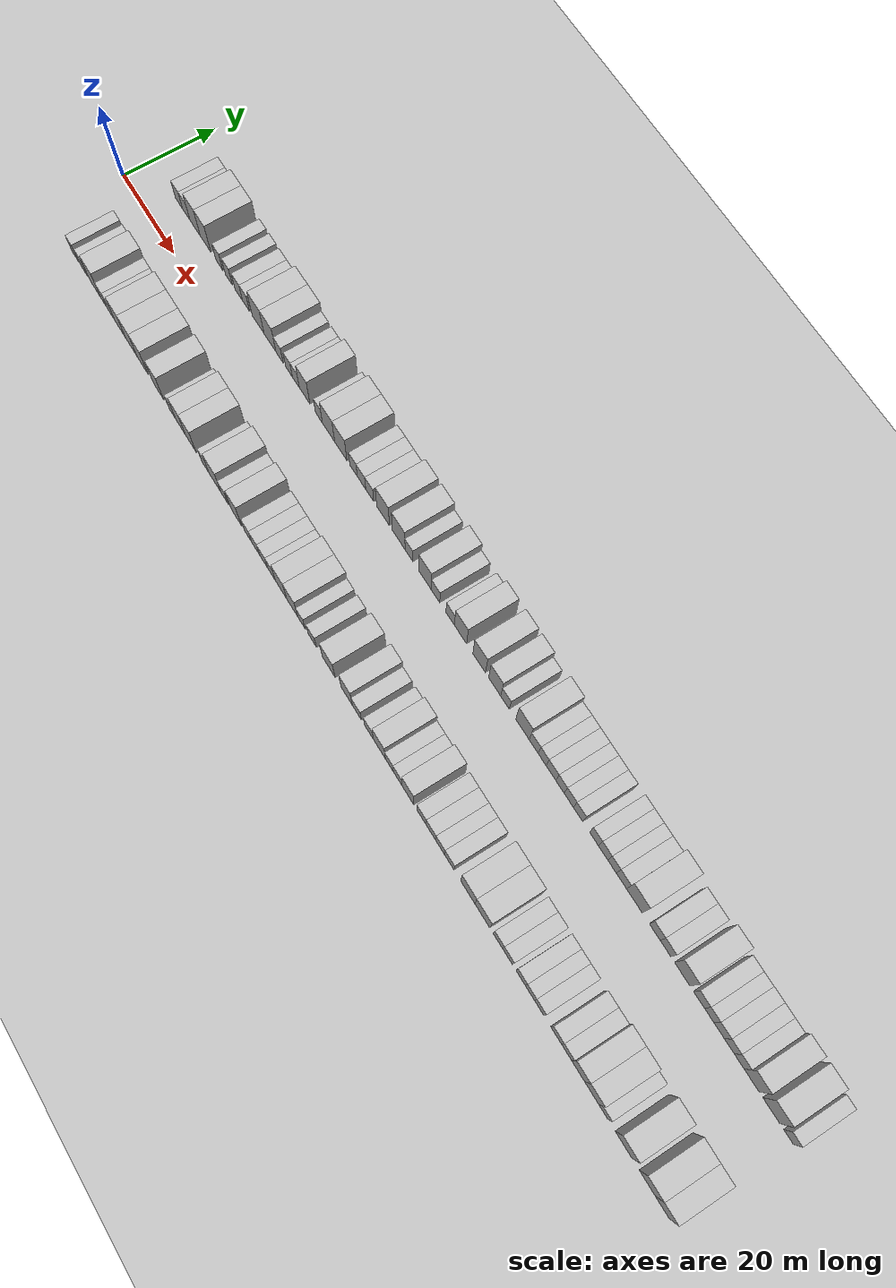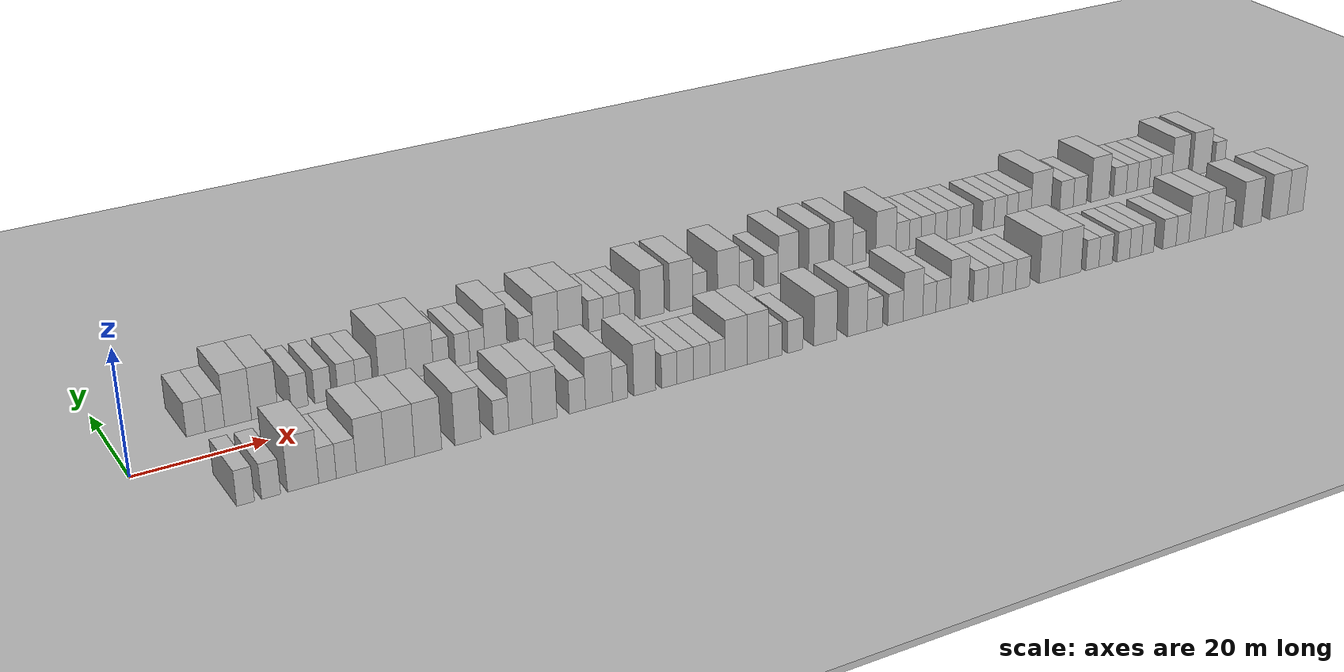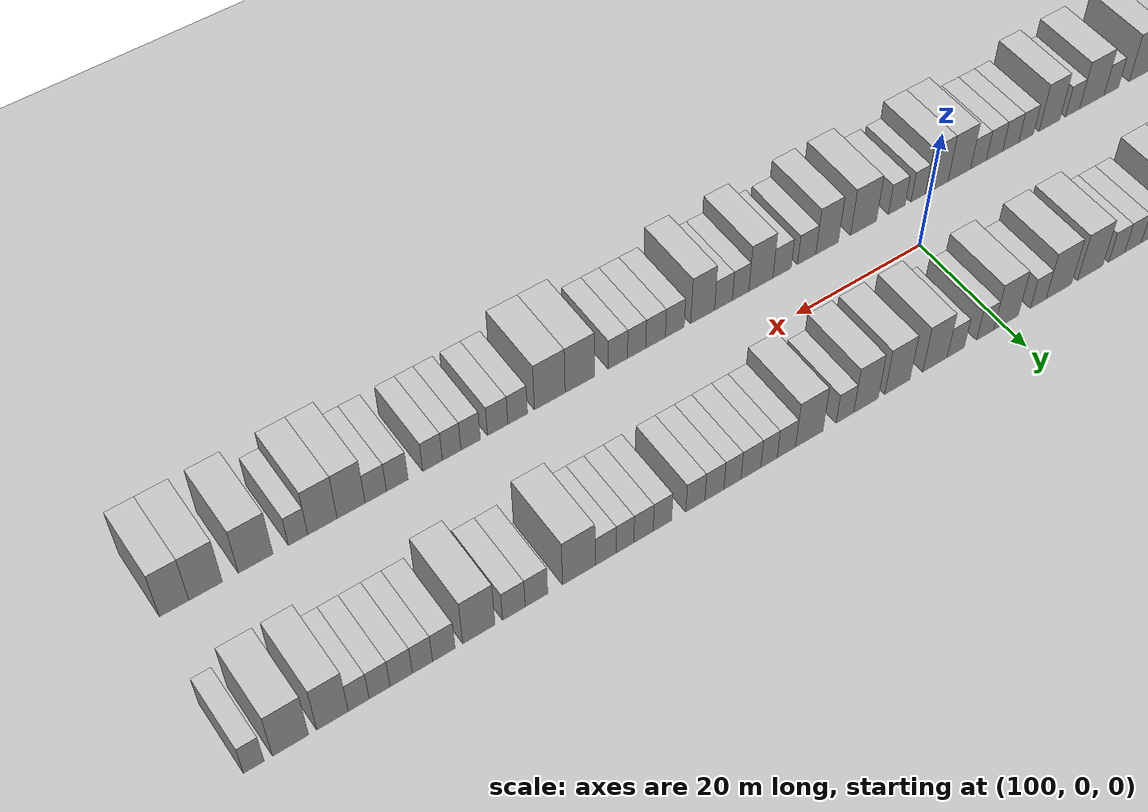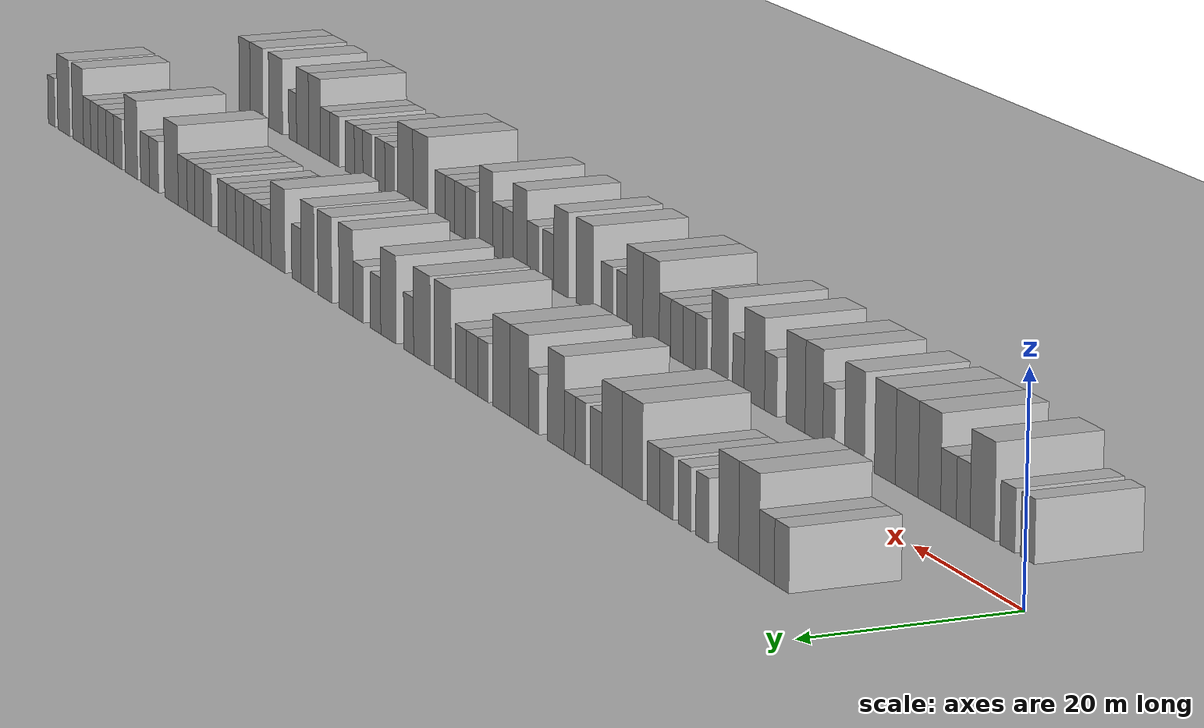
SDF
<?xml version="1.0" encoding="utf-8"?>

<sdf version="1.6">

   <world name="default">

      <gui fullscreen="0">

         <camera name="user_camera">

            <pose>-15 0 4.57585 0 0 0</pose>

            <view_controller>orbit</view_controller>

         </camera>

      </gui>

      <scene>

         <sky>

           <clouds>

             <speed>12</speed>

           </clouds>

         </sky>

         <ambient>0.4 0.4 0.4 1</ambient>

         <background>0.7 0.7 0.7 1</background>

         <shadows>1</shadows>

      </scene>

      <gravity>0 0 -9.8066</gravity>

      <magnetic_field>6e-06 2.3e-05 -4.2e-05</magnetic_field>

      <physics default="0" name="default_physics" type="ode">

         <ode>

            <solver>

               <type>quick</type>

               <iters>10</iters>

               <sor>1.0</sor>

               <use_dynamic_moi_rescaling>0</use_dynamic_moi_rescaling>

            </solver>

            <constraints>

               <cfm>0</cfm>

               <erp>0.2</erp>

               <contact_max_correcting_vel>100</contact_max_correcting_vel>

               <contact_surface_layer>0.001</contact_surface_layer>

            </constraints>

         </ode>

         <max_step_size>0.004</max_step_size>

         <real_time_factor>1</real_time_factor>

         <real_time_update_rate>250</real_time_update_rate>

      </physics>

      <light name="sun" type="directional">

         <cast_shadows>1</cast_shadows>

         <pose>0 0 10 0 0 0</pose>

         <diffuse>0.8 0.8 0.8 1</diffuse>

         <specular>0.2 0.2 0.2 1</specular>

         <attenuation>

            <range>1000</range>

            <constant>0.9</constant>

            <linear>0.01</linear>

            <quadratic>0.001</quadratic>

         </attenuation>

         <direction>-0.5 0.1 -0.9</direction>

      </light>

      <include>

         <name>ground_plane_1</name>

         <uri>model://HANNAS_ground_plane</uri>

         <pose>0 0 0  0 0 0</pose>

      </include>

      <include>

         <name>ground_plane_2</name>

         <uri>model://HANNAS_ground_plane</uri>

         <pose>100 0 0  0 0 0</pose>

      </include>

      <model name="building_1">

         <static>1</static>

         <pose frame="">11.3908 11.0000 0 0.000000 0.000000 1.570796</pose>

         <link name="link">

            <pose frame="">0 0 3.00 0 0 0</pose>

            <collision name="collision">

               <geometry>

                  <box>

                     <size>10.0000 2.7816 6.0000</size>

                  </box>

               </geometry>

               <max_contacts>10</max_contacts>

               <surface>

                  <contact>

                     <ode/>

                  </contact>

                  <bounce/>

                  <friction>

                     <torsional>

                        <ode/>

                     </torsional>

                     <ode/>

                  </friction>

               </surface>

            </collision>

            <visual name="visual">

               <cast_shadows>0</cast_shadows>

               <geometry>

                  <box>

                     <size>10.0000 2.7816 6.0000</size>

                  </box>

               </geometry>

               <material>

                  <script>

                     <uri>model://HANNAS_wall/materials/scripts</uri>

                     <uri>model://HANNAS_wall/materials/textures</uri>

                     <name>vrc/HANNAS_wall</name>

                  </script>

               </material>

            </visual>

            <self_collide>0</self_collide>

            <enable_wind>0</enable_wind>

            <kinematic>0</kinematic>

         </link>

      </model>

      <model name="building_2">

         <static>1</static>

         <pose frame="">14.2303 11.0000 0 0.000000 0.000000 1.570796</pose>

         <link name="link">

            <pose frame="">0 0 3.00 0 0 0</pose>

            <collision name="collision">

               <geometry>

                  <box>

                     <size>10.0000 2.8974 6.0000</size>

                  </box>

               </geometry>

               <max_contacts>10</max_contacts>

               <surface>

                  <contact>

                     <ode/>

                  </contact>

                  <bounce/>

                  <friction>

                     <torsional>

                        <ode/>

                     </torsional>

                     <ode/>

                  </friction>

               </surface>

            </collision>

            <visual name="visual">

               <cast_shadows>0</cast_shadows>

               <geometry>

                  <box>

                     <size>10.0000 2.8974 6.0000</size>

                  </box>

               </geometry>

               <material>

                  <script>

                     <uri>model://HANNAS_wall/materials/scripts</uri>

                     <uri>model://HANNAS_wall/materials/textures</uri>

                     <name>vrc/HANNAS_wall</name>

                  </script>

               </material>

            </visual>

            <self_collide>0</self_collide>

            <enable_wind>0</enable_wind>

            <kinematic>0</kinematic>

         </link>

      </model>

      <model name="building_3">

         <static>1</static>

         <pose frame="">17.6931 11.0000 0 0.000000 0.000000 1.570796</pose>

         <link name="link">

            <pose frame="">0 0 4.50 0 0 0</pose>

            <collision name="collision">

               <geometry>

                  <box>

                     <size>10.0000 4.0282 9.0000</size>

                  </box>

               </geometry>

               <max_contacts>10</max_contacts>

               <surface>

                  <contact>

                     <ode/>

                  </contact>

                  <bounce/>

                  <friction>

                     <torsional>

                        <ode/>

                     </torsional>

                     <ode/>

                  </friction>

               </surface>

            </collision>

            <visual name="visual">

               <cast_shadows>0</cast_shadows>

               <geometry>

                  <box>

                     <size>10.0000 4.0282 9.0000</size>

                  </box>

               </geometry>

               <material>

                  <script>

                     <uri>model://HANNAS_wall/materials/scripts</uri>

                     <uri>model://HANNAS_wall/materials/textures</uri>

                     <name>vrc/HANNAS_wall</name>

                  </script>

               </material>

            </visual>

            <self_collide>0</self_collide>

            <enable_wind>0</enable_wind>

            <kinematic>0</kinematic>

         </link>

      </model>

      <model name="building_4">

         <static>1</static>

         <pose frame="">21.7171 11.0000 0 0.000000 0.000000 1.570796</pose>

         <link name="link">

            <pose frame="">0 0 4.50 0 0 0</pose>

            <collision name="collision">

               <geometry>

                  <box>

                     <size>10.0000 4.0198 9.0000</size>

                  </box>

               </geometry>

               <max_contacts>10</max_contacts>

               <surface>

                  <contact>

                     <ode/>

                  </contact>

                  <bounce/>

                  <friction>

                     <torsional>

                        <ode/>

                     </torsional>

                     <ode/>

                  </friction>

               </surface>

            </collision>

            <visual name="visual">

               <cast_shadows>0</cast_shadows>

               <geometry>

                  <box>

                     <size>10.0000 4.0198 9.0000</size>

                  </box>

               </geometry>

               <material>

                  <script>

                     <uri>model://HANNAS_wall/materials/scripts</uri>

                     <uri>model://HANNAS_wall/materials/textures</uri>

                     <name>vrc/HANNAS_wall</name>

                  </script>

               </material>

            </visual>

            <self_collide>0</self_collide>

            <enable_wind>0</enable_wind>

            <kinematic>0</kinematic>

         </link>

      </model>

      <model name="building_5">

         <static>1</static>

         <pose frame="">27.0392 11.0000 0 0.000000 0.000000 1.570796</pose>

         <link name="link">

            <pose frame="">0 0 3.00 0 0 0</pose>

            <collision name="collision">

               <geometry>

                  <box>

                     <size>10.0000 2.6245 6.0000</size>

                  </box>

               </geometry>

               <max_contacts>10</max_contacts>

               <surface>

                  <contact>

                     <ode/>

                  </contact>

                  <bounce/>

                  <friction>

                     <torsional>

                        <ode/>

                     </torsional>

                     <ode/>

                  </friction>

               </surface>

            </collision>

            <visual name="visual">

               <cast_shadows>0</cast_shadows>

               <geometry>

                  <box>

                     <size>10.0000 2.6245 6.0000</size>

                  </box>

               </geometry>

               <material>

                  <script>

                     <uri>model://HANNAS_wall/materials/scripts</uri>

                     <uri>model://HANNAS_wall/materials/textures</uri>

                     <name>vrc/HANNAS_wall</name>

                  </script>

               </material>

            </visual>

            <self_collide>0</self_collide>

            <enable_wind>0</enable_wind>

            <kinematic>0</kinematic>

         </link>

      </model>

      <model name="building_6">

         <static>1</static>

         <pose frame="">30.6633 11.0000 0 0.000000 0.000000 1.570796</pose>

         <link name="link">

            <pose frame="">0 0 3.00 0 0 0</pose>

            <collision name="collision">

               <geometry>

                  <box>

                     <size>10.0000 2.6236 6.0000</size>

                  </box>

               </geometry>

               <max_contacts>10</max_contacts>

               <surface>

                  <contact>

                     <ode/>

                  </contact>

                  <bounce/>

                  <friction>

                     <torsional>

                        <ode/>

                     </torsional>

                     <ode/>

                  </friction>

               </surface>

            </collision>

            <visual name="visual">

               <cast_shadows>0</cast_shadows>

               <geometry>

                  <box>

                     <size>10.0000 2.6236 6.0000</size>

                  </box>

               </geometry>

               <material>

                  <script>

                     <uri>model://HANNAS_wall/materials/scripts</uri>

                     <uri>model://HANNAS_wall/materials/textures</uri>

                     <name>vrc/HANNAS_wall</name>

                  </script>

               </material>

            </visual>

            <self_collide>0</self_collide>

            <enable_wind>0</enable_wind>

            <kinematic>0</kinematic>

         </link>

      </model>

      <model name="building_7">

         <static>1</static>

         <pose frame="">34.3985 11.0000 0 0.000000 0.000000 1.570796</pose>

         <link name="link">

            <pose frame="">0 0 3.00 0 0 0</pose>

            <collision name="collision">

               <geometry>

                  <box>

                     <size>10.0000 2.8468 6.0000</size>

                  </box>

               </geometry>

               <max_contacts>10</max_contacts>

               <surface>

                  <contact>

                     <ode/>

                  </contact>

                  <bounce/>

                  <friction>

                     <torsional>

                        <ode/>

                     </torsional>

                     <ode/>

                  </friction>

               </surface>

            </collision>

            <visual name="visual">

               <cast_shadows>0</cast_shadows>

               <geometry>

                  <box>

                     <size>10.0000 2.8468 6.0000</size>

                  </box>

               </geometry>

               <material>

                  <script>

                     <uri>model://HANNAS_wall/materials/scripts</uri>

                     <uri>model://HANNAS_wall/materials/textures</uri>

                     <name>vrc/HANNAS_wall</name>

                  </script>

               </material>

            </visual>

            <self_collide>0</self_collide>

            <enable_wind>0</enable_wind>

            <kinematic>0</kinematic>

         </link>

      </model>

      <model name="building_8">

         <static>1</static>

         <pose frame="">37.1475 11.0000 0 0.000000 0.000000 1.570796</pose>

         <link name="link">

            <pose frame="">0 0 3.00 0 0 0</pose>

            <collision name="collision">

               <geometry>

                  <box>

                     <size>10.0000 2.6512 6.0000</size>

                  </box>

               </geometry>

               <max_contacts>10</max_contacts>

               <surface>

                  <contact>

                     <ode/>

                  </contact>

                  <bounce/>

                  <friction>

                     <torsional>

                        <ode/>

                     </torsional>

                     <ode/>

                  </friction>

               </surface>

            </collision>

            <visual name="visual">

               <cast_shadows>0</cast_shadows>

               <geometry>

                  <box>

                     <size>10.0000 2.6512 6.0000</size>

                  </box>

               </geometry>

               <material>

                  <script>

                     <uri>model://HANNAS_wall/materials/scripts</uri>

                     <uri>model://HANNAS_wall/materials/textures</uri>

                     <name>vrc/HANNAS_wall</name>

                  </script>

               </material>

            </visual>

            <self_collide>0</self_collide>

            <enable_wind>0</enable_wind>

            <kinematic>0</kinematic>

         </link>

      </model>

      <model name="building_9">

         <static>1</static>

         <pose frame="">41.6836 11.0000 0 0.000000 0.000000 1.570796</pose>

         <link name="link">

            <pose frame="">0 0 4.50 0 0 0</pose>

            <collision name="collision">

               <geometry>

                  <box>

                     <size>10.0000 4.4210 9.0000</size>

                  </box>

               </geometry>

               <max_contacts>10</max_contacts>

               <surface>

                  <contact>

                     <ode/>

                  </contact>

                  <bounce/>

                  <friction>

                     <torsional>

                        <ode/>

                     </torsional>

                     <ode/>

                  </friction>

               </surface>

            </collision>

            <visual name="visual">

               <cast_shadows>0</cast_shadows>

               <geometry>

                  <box>

                     <size>10.0000 4.4210 9.0000</size>

                  </box>

               </geometry>

               <material>

                  <script>

                     <uri>model://HANNAS_wall/materials/scripts</uri>

                     <uri>model://HANNAS_wall/materials/textures</uri>

                     <name>vrc/HANNAS_wall</name>

                  </script>

               </material>

            </visual>

            <self_collide>0</self_collide>

            <enable_wind>0</enable_wind>

            <kinematic>0</kinematic>

         </link>

      </model>

      <model name="building_10">

         <static>1</static>

         <pose frame="">46.0706 11.0000 0 0.000000 0.000000 1.570796</pose>

         <link name="link">

            <pose frame="">0 0 4.50 0 0 0</pose>

            <collision name="collision">

               <geometry>

                  <box>

                     <size>10.0000 4.3528 9.0000</size>

                  </box>

               </geometry>

               <max_contacts>10</max_contacts>

               <surface>

                  <contact>

                     <ode/>

                  </contact>

                  <bounce/>

                  <friction>

                     <torsional>

                        <ode/>

                     </torsional>

                     <ode/>

                  </friction>

               </surface>

            </collision>

            <visual name="visual">

               <cast_shadows>0</cast_shadows>

               <geometry>

                  <box>

                     <size>10.0000 4.3528 9.0000</size>

                  </box>

               </geometry>

               <material>

                  <script>

                     <uri>model://HANNAS_wall/materials/scripts</uri>

                     <uri>model://HANNAS_wall/materials/textures</uri>

                     <name>vrc/HANNAS_wall</name>

                  </script>

               </material>

            </visual>

            <self_collide>0</self_collide>

            <enable_wind>0</enable_wind>

            <kinematic>0</kinematic>

         </link>

      </model>

      <model name="building_11">

         <static>1</static>

         <pose frame="">49.5463 11.0000 0 0.000000 0.000000 1.570796</pose>

         <link name="link">

            <pose frame="">0 0 3.00 0 0 0</pose>

            <collision name="collision">

               <geometry>

                  <box>

                     <size>10.0000 2.5986 6.0000</size>

                  </box>

               </geometry>

               <max_contacts>10</max_contacts>

               <surface>

                  <contact>

                     <ode/>

                  </contact>

                  <bounce/>

                  <friction>

                     <torsional>

                        <ode/>

                     </torsional>

                     <ode/>

                  </friction>

               </surface>

            </collision>

            <visual name="visual">

               <cast_shadows>0</cast_shadows>

               <geometry>

                  <box>

                     <size>10.0000 2.5986 6.0000</size>

                  </box>

               </geometry>

               <material>

                  <script>

                     <uri>model://HANNAS_wall/materials/scripts</uri>

                     <uri>model://HANNAS_wall/materials/textures</uri>

                     <name>vrc/HANNAS_wall</name>

                  </script>

               </material>

            </visual>

            <self_collide>0</self_collide>

            <enable_wind>0</enable_wind>

            <kinematic>0</kinematic>

         </link>

      </model>

      <model name="building_12">

         <static>1</static>

         <pose frame="">53.0524 11.0000 0 0.000000 0.000000 1.570796</pose>

         <link name="link">

            <pose frame="">0 0 3.00 0 0 0</pose>

            <collision name="collision">

               <geometry>

                  <box>

                     <size>10.0000 2.4136 6.0000</size>

                  </box>

               </geometry>

               <max_contacts>10</max_contacts>

               <surface>

                  <contact>

                     <ode/>

                  </contact>

                  <bounce/>

                  <friction>

                     <torsional>

                        <ode/>

                     </torsional>

                     <ode/>

                  </friction>

               </surface>

            </collision>

            <visual name="visual">

               <cast_shadows>0</cast_shadows>

               <geometry>

                  <box>

                     <size>10.0000 2.4136 6.0000</size>

                  </box>

               </geometry>

               <material>

                  <script>

                     <uri>model://HANNAS_wall/materials/scripts</uri>

                     <uri>model://HANNAS_wall/materials/textures</uri>

                     <name>vrc/HANNAS_wall</name>

                  </script>

               </material>

            </visual>

            <self_collide>0</self_collide>

            <enable_wind>0</enable_wind>

            <kinematic>0</kinematic>

         </link>

      </model>

      <model name="building_13">

         <static>1</static>

         <pose frame="">55.4988 11.0000 0 0.000000 0.000000 1.570796</pose>

         <link name="link">

            <pose frame="">0 0 3.00 0 0 0</pose>

            <collision name="collision">

               <geometry>

                  <box>

                     <size>10.0000 2.4793 6.0000</size>

                  </box>

               </geometry>

               <max_contacts>10</max_contacts>

               <surface>

                  <contact>

                     <ode/>

                  </contact>

                  <bounce/>

                  <friction>

                     <torsional>

                        <ode/>

                     </torsional>

                     <ode/>

                  </friction>

               </surface>

            </collision>

            <visual name="visual">

               <cast_shadows>0</cast_shadows>

               <geometry>

                  <box>

                     <size>10.0000 2.4793 6.0000</size>

                  </box>

               </geometry>

               <material>

                  <script>

                     <uri>model://HANNAS_wall/materials/scripts</uri>

                     <uri>model://HANNAS_wall/materials/textures</uri>

                     <name>vrc/HANNAS_wall</name>

                  </script>

               </material>

            </visual>

            <self_collide>0</self_collide>

            <enable_wind>0</enable_wind>

            <kinematic>0</kinematic>

         </link>

      </model>

      <model name="building_14">

         <static>1</static>

         <pose frame="">58.6206 11.0000 0 0.000000 0.000000 1.570796</pose>

         <link name="link">

            <pose frame="">0 0 4.50 0 0 0</pose>

            <collision name="collision">

               <geometry>

                  <box>

                     <size>10.0000 3.7642 9.0000</size>

                  </box>

               </geometry>

               <max_contacts>10</max_contacts>

               <surface>

                  <contact>

                     <ode/>

                  </contact>

                  <bounce/>

                  <friction>

                     <torsional>

                        <ode/>

                     </torsional>

                     <ode/>

                  </friction>

               </surface>

            </collision>

            <visual name="visual">

               <cast_shadows>0</cast_shadows>

               <geometry>

                  <box>

                     <size>10.0000 3.7642 9.0000</size>

                  </box>

               </geometry>

               <material>

                  <script>

                     <uri>model://HANNAS_wall/materials/scripts</uri>

                     <uri>model://HANNAS_wall/materials/textures</uri>

                     <name>vrc/HANNAS_wall</name>

                  </script>

               </material>

            </visual>

            <self_collide>0</self_collide>

            <enable_wind>0</enable_wind>

            <kinematic>0</kinematic>

         </link>

      </model>

      <model name="building_15">

         <static>1</static>

         <pose frame="">63.7367 11.0000 0 0.000000 0.000000 1.570796</pose>

         <link name="link">

            <pose frame="">0 0 3.00 0 0 0</pose>

            <collision name="collision">

               <geometry>

                  <box>

                     <size>10.0000 2.4681 6.0000</size>

                  </box>

               </geometry>

               <max_contacts>10</max_contacts>

               <surface>

                  <contact>

                     <ode/>

                  </contact>

                  <bounce/>

                  <friction>

                     <torsional>

                        <ode/>

                     </torsional>

                     <ode/>

                  </friction>

               </surface>

            </collision>

            <visual name="visual">

               <cast_shadows>0</cast_shadows>

               <geometry>

                  <box>

                     <size>10.0000 2.4681 6.0000</size>

                  </box>

               </geometry>

               <material>

                  <script>

                     <uri>model://HANNAS_wall/materials/scripts</uri>

                     <uri>model://HANNAS_wall/materials/textures</uri>

                     <name>vrc/HANNAS_wall</name>

                  </script>

               </material>

            </visual>

            <self_collide>0</self_collide>

            <enable_wind>0</enable_wind>

            <kinematic>0</kinematic>

         </link>

      </model>

      <model name="building_16">

         <static>1</static>

         <pose frame="">67.1191 11.0000 0 0.000000 0.000000 1.570796</pose>

         <link name="link">

            <pose frame="">0 0 4.50 0 0 0</pose>

            <collision name="collision">

               <geometry>

                  <box>

                     <size>10.0000 4.2967 9.0000</size>

                  </box>

               </geometry>

               <max_contacts>10</max_contacts>

               <surface>

                  <contact>

                     <ode/>

                  </contact>

                  <bounce/>

                  <friction>

                     <torsional>

                        <ode/>

                     </torsional>

                     <ode/>

                  </friction>

               </surface>

            </collision>

            <visual name="visual">

               <cast_shadows>0</cast_shadows>

               <geometry>

                  <box>

                     <size>10.0000 4.2967 9.0000</size>

                  </box>

               </geometry>

               <material>

                  <script>

                     <uri>model://HANNAS_wall/materials/scripts</uri>

                     <uri>model://HANNAS_wall/materials/textures</uri>

                     <name>vrc/HANNAS_wall</name>

                  </script>

               </material>

            </visual>

            <self_collide>0</self_collide>

            <enable_wind>0</enable_wind>

            <kinematic>0</kinematic>

         </link>

      </model>

      <model name="building_17">

         <static>1</static>

         <pose frame="">71.3927 11.0000 0 0.000000 0.000000 1.570796</pose>

         <link name="link">

            <pose frame="">0 0 4.50 0 0 0</pose>

            <collision name="collision">

               <geometry>

                  <box>

                     <size>10.0000 4.2505 9.0000</size>

                  </box>

               </geometry>

               <max_contacts>10</max_contacts>

               <surface>

                  <contact>

                     <ode/>

                  </contact>

                  <bounce/>

                  <friction>

                     <torsional>

                        <ode/>

                     </torsional>

                     <ode/>

                  </friction>

               </surface>

            </collision>

            <visual name="visual">

               <cast_shadows>0</cast_shadows>

               <geometry>

                  <box>

                     <size>10.0000 4.2505 9.0000</size>

                  </box>

               </geometry>

               <material>

                  <script>

                     <uri>model://HANNAS_wall/materials/scripts</uri>

                     <uri>model://HANNAS_wall/materials/textures</uri>

                     <name>vrc/HANNAS_wall</name>

                  </script>

               </material>

            </visual>

            <self_collide>0</self_collide>

            <enable_wind>0</enable_wind>

            <kinematic>0</kinematic>

         </link>

      </model>

      <model name="building_18">

         <static>1</static>

         <pose frame="">75.8193 11.0000 0 0.000000 0.000000 1.570796</pose>

         <link name="link">

            <pose frame="">0 0 3.00 0 0 0</pose>

            <collision name="collision">

               <geometry>

                  <box>

                     <size>10.0000 2.6027 6.0000</size>

                  </box>

               </geometry>

               <max_contacts>10</max_contacts>

               <surface>

                  <contact>

                     <ode/>

                  </contact>

                  <bounce/>

                  <friction>

                     <torsional>

                        <ode/>

                     </torsional>

                     <ode/>

                  </friction>

               </surface>

            </collision>

            <visual name="visual">

               <cast_shadows>0</cast_shadows>

               <geometry>

                  <box>

                     <size>10.0000 2.6027 6.0000</size>

                  </box>

               </geometry>

               <material>

                  <script>

                     <uri>model://HANNAS_wall/materials/scripts</uri>

                     <uri>model://HANNAS_wall/materials/textures</uri>

                     <name>vrc/HANNAS_wall</name>

                  </script>

               </material>

            </visual>

            <self_collide>0</self_collide>

            <enable_wind>0</enable_wind>

            <kinematic>0</kinematic>

         </link>

      </model>

      <model name="building_19">

         <static>1</static>

         <pose frame="">78.5585 11.0000 0 0.000000 0.000000 1.570796</pose>

         <link name="link">

            <pose frame="">0 0 3.00 0 0 0</pose>

            <collision name="collision">

               <geometry>

                  <box>

                     <size>10.0000 2.8757 6.0000</size>

                  </box>

               </geometry>

               <max_contacts>10</max_contacts>

               <surface>

                  <contact>

                     <ode/>

                  </contact>

                  <bounce/>

                  <friction>

                     <torsional>

                        <ode/>

                     </torsional>

                     <ode/>

                  </friction>

               </surface>

            </collision>

            <visual name="visual">

               <cast_shadows>0</cast_shadows>

               <geometry>

                  <box>

                     <size>10.0000 2.8757 6.0000</size>

                  </box>

               </geometry>

               <material>

                  <script>

                     <uri>model://HANNAS_wall/materials/scripts</uri>

                     <uri>model://HANNAS_wall/materials/textures</uri>

                     <name>vrc/HANNAS_wall</name>

                  </script>

               </material>

            </visual>

            <self_collide>0</self_collide>

            <enable_wind>0</enable_wind>

            <kinematic>0</kinematic>

         </link>

      </model>

      <model name="building_20">

         <static>1</static>

         <pose frame="">81.3552 11.0000 0 0.000000 0.000000 1.570796</pose>

         <link name="link">

            <pose frame="">0 0 3.00 0 0 0</pose>

            <collision name="collision">

               <geometry>

                  <box>

                     <size>10.0000 2.7176 6.0000</size>

                  </box>

               </geometry>

               <max_contacts>10</max_contacts>

               <surface>

                  <contact>

                     <ode/>

                  </contact>

                  <bounce/>

                  <friction>

                     <torsional>

                        <ode/>

                     </torsional>

                     <ode/>

                  </friction>

               </surface>

            </collision>

            <visual name="visual">

               <cast_shadows>0</cast_shadows>

               <geometry>

                  <box>

                     <size>10.0000 2.7176 6.0000</size>

                  </box>

               </geometry>

               <material>

                  <script>

                     <uri>model://HANNAS_wall/materials/scripts</uri>

                     <uri>model://HANNAS_wall/materials/textures</uri>

                     <name>vrc/HANNAS_wall</name>

                  </script>

               </material>

            </visual>

            <self_collide>0</self_collide>

            <enable_wind>0</enable_wind>

            <kinematic>0</kinematic>

         </link>

      </model>

      <model name="building_21">

         <static>1</static>

         <pose frame="">85.8590 11.0000 0 0.000000 0.000000 1.570796</pose>

         <link name="link">

            <pose frame="">0 0 4.50 0 0 0</pose>

            <collision name="collision">

               <geometry>

                  <box>

                     <size>10.0000 4.2899 9.0000</size>

                  </box>

               </geometry>

               <max_contacts>10</max_contacts>

               <surface>

                  <contact>

                     <ode/>

                  </contact>

                  <bounce/>

                  <friction>

                     <torsional>

                        <ode/>

                     </torsional>

                     <ode/>

                  </friction>

               </surface>

            </collision>

            <visual name="visual">

               <cast_shadows>0</cast_shadows>

               <geometry>

                  <box>

                     <size>10.0000 4.2899 9.0000</size>

                  </box>

               </geometry>

               <material>

                  <script>

                     <uri>model://HANNAS_wall/materials/scripts</uri>

                     <uri>model://HANNAS_wall/materials/textures</uri>

                     <name>vrc/HANNAS_wall</name>

                  </script>

               </material>

            </visual>

            <self_collide>0</self_collide>

            <enable_wind>0</enable_wind>

            <kinematic>0</kinematic>

         </link>

      </model>

      <model name="building_22">

         <static>1</static>

         <pose frame="">91.1369 11.0000 0 0.000000 0.000000 1.570796</pose>

         <link name="link">

            <pose frame="">0 0 4.50 0 0 0</pose>

            <collision name="collision">

               <geometry>

                  <box>

                     <size>10.0000 4.2660 9.0000</size>

                  </box>

               </geometry>

               <max_contacts>10</max_contacts>

               <surface>

                  <contact>

                     <ode/>

                  </contact>

                  <bounce/>

                  <friction>

                     <torsional>

                        <ode/>

                     </torsional>

                     <ode/>

                  </friction>

               </surface>

            </collision>

            <visual name="visual">

               <cast_shadows>0</cast_shadows>

               <geometry>

                  <box>

                     <size>10.0000 4.2660 9.0000</size>

                  </box>

               </geometry>

               <material>

                  <script>

                     <uri>model://HANNAS_wall/materials/scripts</uri>

                     <uri>model://HANNAS_wall/materials/textures</uri>

                     <name>vrc/HANNAS_wall</name>

                  </script>

               </material>

            </visual>

            <self_collide>0</self_collide>

            <enable_wind>0</enable_wind>

            <kinematic>0</kinematic>

         </link>

      </model>

      <model name="building_23">

         <static>1</static>

         <pose frame="">94.5682 11.0000 0 0.000000 0.000000 1.570796</pose>

         <link name="link">

            <pose frame="">0 0 3.00 0 0 0</pose>

            <collision name="collision">

               <geometry>

                  <box>

                     <size>10.0000 2.5964 6.0000</size>

                  </box>

               </geometry>

               <max_contacts>10</max_contacts>

               <surface>

                  <contact>

                     <ode/>

                  </contact>

                  <bounce/>

                  <friction>

                     <torsional>

                        <ode/>

                     </torsional>

                     <ode/>

                  </friction>

               </surface>

            </collision>

            <visual name="visual">

               <cast_shadows>0</cast_shadows>

               <geometry>

                  <box>

                     <size>10.0000 2.5964 6.0000</size>

                  </box>

               </geometry>

               <material>

                  <script>

                     <uri>model://HANNAS_wall/materials/scripts</uri>

                     <uri>model://HANNAS_wall/materials/textures</uri>

                     <name>vrc/HANNAS_wall</name>

                  </script>

               </material>

            </visual>

            <self_collide>0</self_collide>

            <enable_wind>0</enable_wind>

            <kinematic>0</kinematic>

         </link>

      </model>

      <model name="building_24">

         <static>1</static>

         <pose frame="">99.8777 11.0000 0 0.000000 0.000000 1.570796</pose>

         <link name="link">

            <pose frame="">0 0 4.50 0 0 0</pose>

            <collision name="collision">

               <geometry>

                  <box>

                     <size>10.0000 4.0226 9.0000</size>

                  </box>

               </geometry>

               <max_contacts>10</max_contacts>

               <surface>

                  <contact>

                     <ode/>

                  </contact>

                  <bounce/>

                  <friction>

                     <torsional>

                        <ode/>

                     </torsional>

                     <ode/>

                  </friction>

               </surface>

            </collision>

            <visual name="visual">

               <cast_shadows>0</cast_shadows>

               <geometry>

                  <box>

                     <size>10.0000 4.0226 9.0000</size>

                  </box>

               </geometry>

               <material>

                  <script>

                     <uri>model://HANNAS_wall/materials/scripts</uri>

                     <uri>model://HANNAS_wall/materials/textures</uri>

                     <name>vrc/HANNAS_wall</name>

                  </script>

               </material>

            </visual>

            <self_collide>0</self_collide>

            <enable_wind>0</enable_wind>

            <kinematic>0</kinematic>

         </link>

      </model>

      <model name="building_25">

         <static>1</static>

         <pose frame="">103.2576 11.0000 0 0.000000 0.000000 1.570796</pose>

         <link name="link">

            <pose frame="">0 0 3.00 0 0 0</pose>

            <collision name="collision">

               <geometry>

                  <box>

                     <size>10.0000 2.7373 6.0000</size>

                  </box>

               </geometry>

               <max_contacts>10</max_contacts>

               <surface>

                  <contact>

                     <ode/>

                  </contact>

                  <bounce/>

                  <friction>

                     <torsional>

                        <ode/>

                     </torsional>

                     <ode/>

                  </friction>

               </surface>

            </collision>

            <visual name="visual">

               <cast_shadows>0</cast_shadows>

               <geometry>

                  <box>

                     <size>10.0000 2.7373 6.0000</size>

                  </box>

               </geometry>

               <material>

                  <script>

                     <uri>model://HANNAS_wall/materials/scripts</uri>

                     <uri>model://HANNAS_wall/materials/textures</uri>

                     <name>vrc/HANNAS_wall</name>

                  </script>

               </material>

            </visual>

            <self_collide>0</self_collide>

            <enable_wind>0</enable_wind>

            <kinematic>0</kinematic>

         </link>

      </model>

      <model name="building_26">

         <static>1</static>

         <pose frame="">107.9982 11.0000 0 0.000000 0.000000 1.570796</pose>

         <link name="link">

            <pose frame="">0 0 3.00 0 0 0</pose>

            <collision name="collision">

               <geometry>

                  <box>

                     <size>10.0000 2.7439 6.0000</size>

                  </box>

               </geometry>

               <max_contacts>10</max_contacts>

               <surface>

                  <contact>

                     <ode/>

                  </contact>

                  <bounce/>

                  <friction>

                     <torsional>

                        <ode/>

                     </torsional>

                     <ode/>

                  </friction>

               </surface>

            </collision>

            <visual name="visual">

               <cast_shadows>0</cast_shadows>

               <geometry>

                  <box>

                     <size>10.0000 2.7439 6.0000</size>

                  </box>

               </geometry>

               <material>

                  <script>

                     <uri>model://HANNAS_wall/materials/scripts</uri>

                     <uri>model://HANNAS_wall/materials/textures</uri>

                     <name>vrc/HANNAS_wall</name>

                  </script>

               </material>

            </visual>

            <self_collide>0</self_collide>

            <enable_wind>0</enable_wind>

            <kinematic>0</kinematic>

         </link>

      </model>

      <model name="building_27">

         <static>1</static>

         <pose frame="">111.3026 11.0000 0 0.000000 0.000000 1.570796</pose>

         <link name="link">

            <pose frame="">0 0 4.50 0 0 0</pose>

            <collision name="collision">

               <geometry>

                  <box>

                     <size>10.0000 3.8650 9.0000</size>

                  </box>

               </geometry>

               <max_contacts>10</max_contacts>

               <surface>

                  <contact>

                     <ode/>

                  </contact>

                  <bounce/>

                  <friction>

                     <torsional>

                        <ode/>

                     </torsional>

                     <ode/>

                  </friction>

               </surface>

            </collision>

            <visual name="visual">

               <cast_shadows>0</cast_shadows>

               <geometry>

                  <box>

                     <size>10.0000 3.8650 9.0000</size>

                  </box>

               </geometry>

               <material>

                  <script>

                     <uri>model://HANNAS_wall/materials/scripts</uri>

                     <uri>model://HANNAS_wall/materials/textures</uri>

                     <name>vrc/HANNAS_wall</name>

                  </script>

               </material>

            </visual>

            <self_collide>0</self_collide>

            <enable_wind>0</enable_wind>

            <kinematic>0</kinematic>

         </link>

      </model>

      <model name="building_28">

         <static>1</static>

         <pose frame="">117.2045 11.0000 0 0.000000 0.000000 1.570796</pose>

         <link name="link">

            <pose frame="">0 0 4.50 0 0 0</pose>

            <collision name="collision">

               <geometry>

                  <box>

                     <size>10.0000 3.9387 9.0000</size>

                  </box>

               </geometry>

               <max_contacts>10</max_contacts>

               <surface>

                  <contact>

                     <ode/>

                  </contact>

                  <bounce/>

                  <friction>

                     <torsional>

                        <ode/>

                     </torsional>

                     <ode/>

                  </friction>

               </surface>

            </collision>

            <visual name="visual">

               <cast_shadows>0</cast_shadows>

               <geometry>

                  <box>

                     <size>10.0000 3.9387 9.0000</size>

                  </box>

               </geometry>

               <material>

                  <script>

                     <uri>model://HANNAS_wall/materials/scripts</uri>

                     <uri>model://HANNAS_wall/materials/textures</uri>

                     <name>vrc/HANNAS_wall</name>

                  </script>

               </material>

            </visual>

            <self_collide>0</self_collide>

            <enable_wind>0</enable_wind>

            <kinematic>0</kinematic>

         </link>

      </model>

      <model name="building_29">

         <static>1</static>

         <pose frame="">122.0515 11.0000 0 0.000000 0.000000 1.570796</pose>

         <link name="link">

            <pose frame="">0 0 4.50 0 0 0</pose>

            <collision name="collision">

               <geometry>

                  <box>

                     <size>10.0000 3.7555 9.0000</size>

                  </box>

               </geometry>

               <max_contacts>10</max_contacts>

               <surface>

                  <contact>

                     <ode/>

                  </contact>

                  <bounce/>

                  <friction>

                     <torsional>

                        <ode/>

                     </torsional>

                     <ode/>

                  </friction>

               </surface>

            </collision>

            <visual name="visual">

               <cast_shadows>0</cast_shadows>

               <geometry>

                  <box>

                     <size>10.0000 3.7555 9.0000</size>

                  </box>

               </geometry>

               <material>

                  <script>

                     <uri>model://HANNAS_wall/materials/scripts</uri>

                     <uri>model://HANNAS_wall/materials/textures</uri>

                     <name>vrc/HANNAS_wall</name>

                  </script>

               </material>

            </visual>

            <self_collide>0</self_collide>

            <enable_wind>0</enable_wind>

            <kinematic>0</kinematic>

         </link>

      </model>

      <model name="building_30">

         <static>1</static>

         <pose frame="">125.2642 11.0000 0 0.000000 0.000000 1.570796</pose>

         <link name="link">

            <pose frame="">0 0 3.00 0 0 0</pose>

            <collision name="collision">

               <geometry>

                  <box>

                     <size>10.0000 2.6699 6.0000</size>

                  </box>

               </geometry>

               <max_contacts>10</max_contacts>

               <surface>

                  <contact>

                     <ode/>

                  </contact>

                  <bounce/>

                  <friction>

                     <torsional>

                        <ode/>

                     </torsional>

                     <ode/>

                  </friction>

               </surface>

            </collision>

            <visual name="visual">

               <cast_shadows>0</cast_shadows>

               <geometry>

                  <box>

                     <size>10.0000 2.6699 6.0000</size>

                  </box>

               </geometry>

               <material>

                  <script>

                     <uri>model://HANNAS_wall/materials/scripts</uri>

                     <uri>model://HANNAS_wall/materials/textures</uri>

                     <name>vrc/HANNAS_wall</name>

                  </script>

               </material>

            </visual>

            <self_collide>0</self_collide>

            <enable_wind>0</enable_wind>

            <kinematic>0</kinematic>

         </link>

      </model>

      <model name="building_31">

         <static>1</static>

         <pose frame="">130.6579 11.0000 0 0.000000 0.000000 1.570796</pose>

         <link name="link">

            <pose frame="">0 0 4.50 0 0 0</pose>

            <collision name="collision">

               <geometry>

                  <box>

                     <size>10.0000 4.1175 9.0000</size>

                  </box>

               </geometry>

               <max_contacts>10</max_contacts>

               <surface>

                  <contact>

                     <ode/>

                  </contact>

                  <bounce/>

                  <friction>

                     <torsional>

                        <ode/>

                     </torsional>

                     <ode/>

                  </friction>

               </surface>

            </collision>

            <visual name="visual">

               <cast_shadows>0</cast_shadows>

               <geometry>

                  <box>

                     <size>10.0000 4.1175 9.0000</size>

                  </box>

               </geometry>

               <material>

                  <script>

                     <uri>model://HANNAS_wall/materials/scripts</uri>

                     <uri>model://HANNAS_wall/materials/textures</uri>

                     <name>vrc/HANNAS_wall</name>

                  </script>

               </material>

            </visual>

            <self_collide>0</self_collide>

            <enable_wind>0</enable_wind>

            <kinematic>0</kinematic>

         </link>

      </model>

      <model name="building_32">

         <static>1</static>

         <pose frame="">134.0792 11.0000 0 0.000000 0.000000 1.570796</pose>

         <link name="link">

            <pose frame="">0 0 3.00 0 0 0</pose>

            <collision name="collision">

               <geometry>

                  <box>

                     <size>10.0000 2.7253 6.0000</size>

                  </box>

               </geometry>

               <max_contacts>10</max_contacts>

               <surface>

                  <contact>

                     <ode/>

                  </contact>

                  <bounce/>

                  <friction>

                     <torsional>

                        <ode/>

                     </torsional>

                     <ode/>

                  </friction>

               </surface>

            </collision>

            <visual name="visual">

               <cast_shadows>0</cast_shadows>

               <geometry>

                  <box>

                     <size>10.0000 2.7253 6.0000</size>

                  </box>

               </geometry>

               <material>

                  <script>

                     <uri>model://HANNAS_wall/materials/scripts</uri>

                     <uri>model://HANNAS_wall/materials/textures</uri>

                     <name>vrc/HANNAS_wall</name>

                  </script>

               </material>

            </visual>

            <self_collide>0</self_collide>

            <enable_wind>0</enable_wind>

            <kinematic>0</kinematic>

         </link>

      </model>

      <model name="building_33">

         <static>1</static>

         <pose frame="">136.6524 11.0000 0 0.000000 0.000000 1.570796</pose>

         <link name="link">

            <pose frame="">0 0 3.00 0 0 0</pose>

            <collision name="collision">

               <geometry>

                  <box>

                     <size>10.0000 2.4210 6.0000</size>

                  </box>

               </geometry>

               <max_contacts>10</max_contacts>

               <surface>

                  <contact>

                     <ode/>

                  </contact>

                  <bounce/>

                  <friction>

                     <torsional>

                        <ode/>

                     </torsional>

                     <ode/>

                  </friction>

               </surface>

            </collision>

            <visual name="visual">

               <cast_shadows>0</cast_shadows>

               <geometry>

                  <box>

                     <size>10.0000 2.4210 6.0000</size>

                  </box>

               </geometry>

               <material>

                  <script>

                     <uri>model://HANNAS_wall/materials/scripts</uri>

                     <uri>model://HANNAS_wall/materials/textures</uri>

                     <name>vrc/HANNAS_wall</name>

                  </script>

               </material>

            </visual>

            <self_collide>0</self_collide>

            <enable_wind>0</enable_wind>

            <kinematic>0</kinematic>

         </link>

      </model>

      <model name="building_34">

         <static>1</static>

         <pose frame="">139.3036 11.0000 0 0.000000 0.000000 1.570796</pose>

         <link name="link">

            <pose frame="">0 0 3.00 0 0 0</pose>

            <collision name="collision">

               <geometry>

                  <box>

                     <size>10.0000 2.8814 6.0000</size>

                  </box>

               </geometry>

               <max_contacts>10</max_contacts>

               <surface>

                  <contact>

                     <ode/>

                  </contact>

                  <bounce/>

                  <friction>

                     <torsional>

                        <ode/>

                     </torsional>

                     <ode/>

                  </friction>

               </surface>

            </collision>

            <visual name="visual">

               <cast_shadows>0</cast_shadows>

               <geometry>

                  <box>

                     <size>10.0000 2.8814 6.0000</size>

                  </box>

               </geometry>

               <material>

                  <script>

                     <uri>model://HANNAS_wall/materials/scripts</uri>

                     <uri>model://HANNAS_wall/materials/textures</uri>

                     <name>vrc/HANNAS_wall</name>

                  </script>

               </material>

            </visual>

            <self_collide>0</self_collide>

            <enable_wind>0</enable_wind>

            <kinematic>0</kinematic>

         </link>

      </model>

      <model name="building_35">

         <static>1</static>

         <pose frame="">141.9804 11.0000 0 0.000000 0.000000 1.570796</pose>

         <link name="link">

            <pose frame="">0 0 3.00 0 0 0</pose>

            <collision name="collision">

               <geometry>

                  <box>

                     <size>10.0000 2.4722 6.0000</size>

                  </box>

               </geometry>

               <max_contacts>10</max_contacts>

               <surface>

                  <contact>

                     <ode/>

                  </contact>

                  <bounce/>

                  <friction>

                     <torsional>

                        <ode/>

                     </torsional>

                     <ode/>

                  </friction>

               </surface>

            </collision>

            <visual name="visual">

               <cast_shadows>0</cast_shadows>

               <geometry>

                  <box>

                     <size>10.0000 2.4722 6.0000</size>

                  </box>

               </geometry>

               <material>

                  <script>

                     <uri>model://HANNAS_wall/materials/scripts</uri>

                     <uri>model://HANNAS_wall/materials/textures</uri>

                     <name>vrc/HANNAS_wall</name>

                  </script>

               </material>

            </visual>

            <self_collide>0</self_collide>

            <enable_wind>0</enable_wind>

            <kinematic>0</kinematic>

         </link>

      </model>

      <model name="building_36">

         <static>1</static>

         <pose frame="">144.5878 11.0000 0 0.000000 0.000000 1.570796</pose>

         <link name="link">

            <pose frame="">0 0 3.00 0 0 0</pose>

            <collision name="collision">

               <geometry>

                  <box>

                     <size>10.0000 2.7424 6.0000</size>

                  </box>

               </geometry>

               <max_contacts>10</max_contacts>

               <surface>

                  <contact>

                     <ode/>

                  </contact>

                  <bounce/>

                  <friction>

                     <torsional>

                        <ode/>

                     </torsional>

                     <ode/>

                  </friction>

               </surface>

            </collision>

            <visual name="visual">

               <cast_shadows>0</cast_shadows>

               <geometry>

                  <box>

                     <size>10.0000 2.7424 6.0000</size>

                  </box>

               </geometry>

               <material>

                  <script>

                     <uri>model://HANNAS_wall/materials/scripts</uri>

                     <uri>model://HANNAS_wall/materials/textures</uri>

                     <name>vrc/HANNAS_wall</name>

                  </script>

               </material>

            </visual>

            <self_collide>0</self_collide>

            <enable_wind>0</enable_wind>

            <kinematic>0</kinematic>

         </link>

      </model>

      <model name="building_37">

         <static>1</static>

         <pose frame="">147.3143 11.0000 0 0.000000 0.000000 1.570796</pose>

         <link name="link">

            <pose frame="">0 0 3.00 0 0 0</pose>

            <collision name="collision">

               <geometry>

                  <box>

                     <size>10.0000 2.7106 6.0000</size>

                  </box>

               </geometry>

               <max_contacts>10</max_contacts>

               <surface>

                  <contact>

                     <ode/>

                  </contact>

                  <bounce/>

                  <friction>

                     <torsional>

                        <ode/>

                     </torsional>

                     <ode/>

                  </friction>

               </surface>

            </collision>

            <visual name="visual">

               <cast_shadows>0</cast_shadows>

               <geometry>

                  <box>

                     <size>10.0000 2.7106 6.0000</size>

                  </box>

               </geometry>

               <material>

                  <script>

                     <uri>model://HANNAS_wall/materials/scripts</uri>

                     <uri>model://HANNAS_wall/materials/textures</uri>

                     <name>vrc/HANNAS_wall</name>

                  </script>

               </material>

            </visual>

            <self_collide>0</self_collide>

            <enable_wind>0</enable_wind>

            <kinematic>0</kinematic>

         </link>

      </model>

      <model name="building_38">

         <static>1</static>

         <pose frame="">151.9646 11.0000 0 0.000000 0.000000 1.570796</pose>

         <link name="link">

            <pose frame="">0 0 3.00 0 0 0</pose>

            <collision name="collision">

               <geometry>

                  <box>

                     <size>10.0000 2.5902 6.0000</size>

                  </box>

               </geometry>

               <max_contacts>10</max_contacts>

               <surface>

                  <contact>

                     <ode/>

                  </contact>

                  <bounce/>

                  <friction>

                     <torsional>

                        <ode/>

                     </torsional>

                     <ode/>

                  </friction>

               </surface>

            </collision>

            <visual name="visual">

               <cast_shadows>0</cast_shadows>

               <geometry>

                  <box>

                     <size>10.0000 2.5902 6.0000</size>

                  </box>

               </geometry>

               <material>

                  <script>

                     <uri>model://HANNAS_wall/materials/scripts</uri>

                     <uri>model://HANNAS_wall/materials/textures</uri>

                     <name>vrc/HANNAS_wall</name>

                  </script>

               </material>

            </visual>

            <self_collide>0</self_collide>

            <enable_wind>0</enable_wind>

            <kinematic>0</kinematic>

         </link>

      </model>

      <model name="building_39">

         <static>1</static>

         <pose frame="">154.6111 11.0000 0 0.000000 0.000000 1.570796</pose>

         <link name="link">

            <pose frame="">0 0 3.00 0 0 0</pose>

            <collision name="collision">

               <geometry>

                  <box>

                     <size>10.0000 2.7027 6.0000</size>

                  </box>

               </geometry>

               <max_contacts>10</max_contacts>

               <surface>

                  <contact>

                     <ode/>

                  </contact>

                  <bounce/>

                  <friction>

                     <torsional>

                        <ode/>

                     </torsional>

                     <ode/>

                  </friction>

               </surface>

            </collision>

            <visual name="visual">

               <cast_shadows>0</cast_shadows>

               <geometry>

                  <box>

                     <size>10.0000 2.7027 6.0000</size>

                  </box>

               </geometry>

               <material>

                  <script>

                     <uri>model://HANNAS_wall/materials/scripts</uri>

                     <uri>model://HANNAS_wall/materials/textures</uri>

                     <name>vrc/HANNAS_wall</name>

                  </script>

               </material>

            </visual>

            <self_collide>0</self_collide>

            <enable_wind>0</enable_wind>

            <kinematic>0</kinematic>

         </link>

      </model>

      <model name="building_40">

         <static>1</static>

         <pose frame="">157.1853 11.0000 0 0.000000 0.000000 1.570796</pose>

         <link name="link">

            <pose frame="">0 0 3.00 0 0 0</pose>

            <collision name="collision">

               <geometry>

                  <box>

                     <size>10.0000 2.4456 6.0000</size>

                  </box>

               </geometry>

               <max_contacts>10</max_contacts>

               <surface>

                  <contact>

                     <ode/>

                  </contact>

                  <bounce/>

                  <friction>

                     <torsional>

                        <ode/>

                     </torsional>

                     <ode/>

                  </friction>

               </surface>

            </collision>

            <visual name="visual">

               <cast_shadows>0</cast_shadows>

               <geometry>

                  <box>

                     <size>10.0000 2.4456 6.0000</size>

                  </box>

               </geometry>

               <material>

                  <script>

                     <uri>model://HANNAS_wall/materials/scripts</uri>

                     <uri>model://HANNAS_wall/materials/textures</uri>

                     <name>vrc/HANNAS_wall</name>

                  </script>

               </material>

            </visual>

            <self_collide>0</self_collide>

            <enable_wind>0</enable_wind>

            <kinematic>0</kinematic>

         </link>

      </model>

      <model name="building_41">

         <static>1</static>

         <pose frame="">159.8622 11.0000 0 0.000000 0.000000 1.570796</pose>

         <link name="link">

            <pose frame="">0 0 3.00 0 0 0</pose>

            <collision name="collision">

               <geometry>

                  <box>

                     <size>10.0000 2.9083 6.0000</size>

                  </box>

               </geometry>

               <max_contacts>10</max_contacts>

               <surface>

                  <contact>

                     <ode/>

                  </contact>

                  <bounce/>

                  <friction>

                     <torsional>

                        <ode/>

                     </torsional>

                     <ode/>

                  </friction>

               </surface>

            </collision>

            <visual name="visual">

               <cast_shadows>0</cast_shadows>

               <geometry>

                  <box>

                     <size>10.0000 2.9083 6.0000</size>

                  </box>

               </geometry>

               <material>

                  <script>

                     <uri>model://HANNAS_wall/materials/scripts</uri>

                     <uri>model://HANNAS_wall/materials/textures</uri>

                     <name>vrc/HANNAS_wall</name>

                  </script>

               </material>

            </visual>

            <self_collide>0</self_collide>

            <enable_wind>0</enable_wind>

            <kinematic>0</kinematic>

         </link>

      </model>

      <model name="building_42">

         <static>1</static>

         <pose frame="">163.5277 11.0000 0 0.000000 0.000000 1.570796</pose>

         <link name="link">

            <pose frame="">0 0 4.50 0 0 0</pose>

            <collision name="collision">

               <geometry>

                  <box>

                     <size>10.0000 4.4227 9.0000</size>

                  </box>

               </geometry>

               <max_contacts>10</max_contacts>

               <surface>

                  <contact>

                     <ode/>

                  </contact>

                  <bounce/>

                  <friction>

                     <torsional>

                        <ode/>

                     </torsional>

                     <ode/>

                  </friction>

               </surface>

            </collision>

            <visual name="visual">

               <cast_shadows>0</cast_shadows>

               <geometry>

                  <box>

                     <size>10.0000 4.4227 9.0000</size>

                  </box>

               </geometry>

               <material>

                  <script>

                     <uri>model://HANNAS_wall/materials/scripts</uri>

                     <uri>model://HANNAS_wall/materials/textures</uri>

                     <name>vrc/HANNAS_wall</name>

                  </script>

               </material>

            </visual>

            <self_collide>0</self_collide>

            <enable_wind>0</enable_wind>

            <kinematic>0</kinematic>

         </link>

      </model>

      <model name="building_43">

         <static>1</static>

         <pose frame="">169.2356 11.0000 0 0.000000 0.000000 1.570796</pose>

         <link name="link">

            <pose frame="">0 0 3.00 0 0 0</pose>

            <collision name="collision">

               <geometry>

                  <box>

                     <size>10.0000 2.9930 6.0000</size>

                  </box>

               </geometry>

               <max_contacts>10</max_contacts>

               <surface>

                  <contact>

                     <ode/>

                  </contact>

                  <bounce/>

                  <friction>

                     <torsional>

                        <ode/>

                     </torsional>

                     <ode/>

                  </friction>

               </surface>

            </collision>

            <visual name="visual">

               <cast_shadows>0</cast_shadows>

               <geometry>

                  <box>

                     <size>10.0000 2.9930 6.0000</size>

                  </box>

               </geometry>

               <material>

                  <script>

                     <uri>model://HANNAS_wall/materials/scripts</uri>

                     <uri>model://HANNAS_wall/materials/textures</uri>

                     <name>vrc/HANNAS_wall</name>

                  </script>

               </material>

            </visual>

            <self_collide>0</self_collide>

            <enable_wind>0</enable_wind>

            <kinematic>0</kinematic>

         </link>

      </model>

      <model name="building_44">

         <static>1</static>

         <pose frame="">172.2272 11.0000 0 0.000000 0.000000 1.570796</pose>

         <link name="link">

            <pose frame="">0 0 3.00 0 0 0</pose>

            <collision name="collision">

               <geometry>

                  <box>

                     <size>10.0000 2.9903 6.0000</size>

                  </box>

               </geometry>

               <max_contacts>10</max_contacts>

               <surface>

                  <contact>

                     <ode/>

                  </contact>

                  <bounce/>

                  <friction>

                     <torsional>

                        <ode/>

                     </torsional>

                     <ode/>

                  </friction>

               </surface>

            </collision>

            <visual name="visual">

               <cast_shadows>0</cast_shadows>

               <geometry>

                  <box>

                     <size>10.0000 2.9903 6.0000</size>

                  </box>

               </geometry>

               <material>

                  <script>

                     <uri>model://HANNAS_wall/materials/scripts</uri>

                     <uri>model://HANNAS_wall/materials/textures</uri>

                     <name>vrc/HANNAS_wall</name>

                  </script>

               </material>

            </visual>

            <self_collide>0</self_collide>

            <enable_wind>0</enable_wind>

            <kinematic>0</kinematic>

         </link>

      </model>

      <model name="building_45">

         <static>1</static>

         <pose frame="">176.8216 11.0000 0 0.000000 0.000000 1.570796</pose>

         <link name="link">

            <pose frame="">0 0 4.50 0 0 0</pose>

            <collision name="collision">

               <geometry>

                  <box>

                     <size>10.0000 4.1985 9.0000</size>

                  </box>

               </geometry>

               <max_contacts>10</max_contacts>

               <surface>

                  <contact>

                     <ode/>

                  </contact>

                  <bounce/>

                  <friction>

                     <torsional>

                        <ode/>

                     </torsional>

                     <ode/>

                  </friction>

               </surface>

            </collision>

            <visual name="visual">

               <cast_shadows>0</cast_shadows>

               <geometry>

                  <box>

                     <size>10.0000 4.1985 9.0000</size>

                  </box>

               </geometry>

               <material>

                  <script>

                     <uri>model://HANNAS_wall/materials/scripts</uri>

                     <uri>model://HANNAS_wall/materials/textures</uri>

                     <name>vrc/HANNAS_wall</name>

                  </script>

               </material>

            </visual>

            <self_collide>0</self_collide>

            <enable_wind>0</enable_wind>

            <kinematic>0</kinematic>

         </link>

      </model>

      <model name="building_46">

         <static>1</static>

         <pose frame="">181.3651 11.0000 0 0.000000 0.000000 1.570796</pose>

         <link name="link">

            <pose frame="">0 0 3.00 0 0 0</pose>

            <collision name="collision">

               <geometry>

                  <box>

                     <size>10.0000 2.8885 6.0000</size>

                  </box>

               </geometry>

               <max_contacts>10</max_contacts>

               <surface>

                  <contact>

                     <ode/>

                  </contact>

                  <bounce/>

                  <friction>

                     <torsional>

                        <ode/>

                     </torsional>

                     <ode/>

                  </friction>

               </surface>

            </collision>

            <visual name="visual">

               <cast_shadows>0</cast_shadows>

               <geometry>

                  <box>

                     <size>10.0000 2.8885 6.0000</size>

                  </box>

               </geometry>

               <material>

                  <script>

                     <uri>model://HANNAS_wall/materials/scripts</uri>

                     <uri>model://HANNAS_wall/materials/textures</uri>

                     <name>vrc/HANNAS_wall</name>

                  </script>

               </material>

            </visual>

            <self_collide>0</self_collide>

            <enable_wind>0</enable_wind>

            <kinematic>0</kinematic>

         </link>

      </model>

      <model name="building_47">

         <static>1</static>

         <pose frame="">184.0944 11.0000 0 0.000000 0.000000 1.570796</pose>

         <link name="link">

            <pose frame="">0 0 3.00 0 0 0</pose>

            <collision name="collision">

               <geometry>

                  <box>

                     <size>10.0000 2.5700 6.0000</size>

                  </box>

               </geometry>

               <max_contacts>10</max_contacts>

               <surface>

                  <contact>

                     <ode/>

                  </contact>

                  <bounce/>

                  <friction>

                     <torsional>

                        <ode/>

                     </torsional>

                     <ode/>

                  </friction>

               </surface>

            </collision>

            <visual name="visual">

               <cast_shadows>0</cast_shadows>

               <geometry>

                  <box>

                     <size>10.0000 2.5700 6.0000</size>

                  </box>

               </geometry>

               <material>

                  <script>

                     <uri>model://HANNAS_wall/materials/scripts</uri>

                     <uri>model://HANNAS_wall/materials/textures</uri>

                     <name>vrc/HANNAS_wall</name>

                  </script>

               </material>

            </visual>

            <self_collide>0</self_collide>

            <enable_wind>0</enable_wind>

            <kinematic>0</kinematic>

         </link>

      </model>

      <model name="building_48">

         <static>1</static>

         <pose frame="">186.7950 11.0000 0 0.000000 0.000000 1.570796</pose>

         <link name="link">

            <pose frame="">0 0 3.00 0 0 0</pose>

            <collision name="collision">

               <geometry>

                  <box>

                     <size>10.0000 2.8314 6.0000</size>

                  </box>

               </geometry>

               <max_contacts>10</max_contacts>

               <surface>

                  <contact>

                     <ode/>

                  </contact>

                  <bounce/>

                  <friction>

                     <torsional>

                        <ode/>

                     </torsional>

                     <ode/>

                  </friction>

               </surface>

            </collision>

            <visual name="visual">

               <cast_shadows>0</cast_shadows>

               <geometry>

                  <box>

                     <size>10.0000 2.8314 6.0000</size>

                  </box>

               </geometry>

               <material>

                  <script>

                     <uri>model://HANNAS_wall/materials/scripts</uri>

                     <uri>model://HANNAS_wall/materials/textures</uri>

                     <name>vrc/HANNAS_wall</name>

                  </script>

               </material>

            </visual>

            <self_collide>0</self_collide>

            <enable_wind>0</enable_wind>

            <kinematic>0</kinematic>

         </link>

      </model>

      <model name="building_49">

         <static>1</static>

         <pose frame="">189.5185 11.0000 0 0.000000 0.000000 1.570796</pose>

         <link name="link">

            <pose frame="">0 0 3.00 0 0 0</pose>

            <collision name="collision">

               <geometry>

                  <box>

                     <size>10.0000 2.6156 6.0000</size>

                  </box>

               </geometry>

               <max_contacts>10</max_contacts>

               <surface>

                  <contact>

                     <ode/>

                  </contact>

                  <bounce/>

                  <friction>

                     <torsional>

                        <ode/>

                     </torsional>

                     <ode/>

                  </friction>

               </surface>

            </collision>

            <visual name="visual">

               <cast_shadows>0</cast_shadows>

               <geometry>

                  <box>

                     <size>10.0000 2.6156 6.0000</size>

                  </box>

               </geometry>

               <material>

                  <script>

                     <uri>model://HANNAS_wall/materials/scripts</uri>

                     <uri>model://HANNAS_wall/materials/textures</uri>

                     <name>vrc/HANNAS_wall</name>

                  </script>

               </material>

            </visual>

            <self_collide>0</self_collide>

            <enable_wind>0</enable_wind>

            <kinematic>0</kinematic>

         </link>

      </model>

      <model name="building_50">

         <static>1</static>

         <pose frame="">192.1290 11.0000 0 0.000000 0.000000 1.570796</pose>

         <link name="link">

            <pose frame="">0 0 3.00 0 0 0</pose>

            <collision name="collision">

               <geometry>

                  <box>

                     <size>10.0000 2.6054 6.0000</size>

                  </box>

               </geometry>

               <max_contacts>10</max_contacts>

               <surface>

                  <contact>

                     <ode/>

                  </contact>

                  <bounce/>

                  <friction>

                     <torsional>

                        <ode/>

                     </torsional>

                     <ode/>

                  </friction>

               </surface>

            </collision>

            <visual name="visual">

               <cast_shadows>0</cast_shadows>

               <geometry>

                  <box>

                     <size>10.0000 2.6054 6.0000</size>

                  </box>

               </geometry>

               <material>

                  <script>

                     <uri>model://HANNAS_wall/materials/scripts</uri>

                     <uri>model://HANNAS_wall/materials/textures</uri>

                     <name>vrc/HANNAS_wall</name>

                  </script>

               </material>

            </visual>

            <self_collide>0</self_collide>

            <enable_wind>0</enable_wind>

            <kinematic>0</kinematic>

         </link>

      </model>

      <model name="building_51">

         <static>1</static>

         <pose frame="">195.3765 11.0000 0 0.000000 0.000000 1.570796</pose>

         <link name="link">

            <pose frame="">0 0 4.50 0 0 0</pose>

            <collision name="collision">

               <geometry>

                  <box>

                     <size>10.0000 3.8895 9.0000</size>

                  </box>

               </geometry>

               <max_contacts>10</max_contacts>

               <surface>

                  <contact>

                     <ode/>

                  </contact>

                  <bounce/>

                  <friction>

                     <torsional>

                        <ode/>

                     </torsional>

                     <ode/>

                  </friction>

               </surface>

            </collision>

            <visual name="visual">

               <cast_shadows>0</cast_shadows>

               <geometry>

                  <box>

                     <size>10.0000 3.8895 9.0000</size>

                  </box>

               </geometry>

               <material>

                  <script>

                     <uri>model://HANNAS_wall/materials/scripts</uri>

                     <uri>model://HANNAS_wall/materials/textures</uri>

                     <name>vrc/HANNAS_wall</name>

                  </script>

               </material>

            </visual>

            <self_collide>0</self_collide>

            <enable_wind>0</enable_wind>

            <kinematic>0</kinematic>

         </link>

      </model>

      <model name="building_52">

         <static>1</static>

         <pose frame="">200.5058 11.0000 0 0.000000 0.000000 1.570796</pose>

         <link name="link">

            <pose frame="">0 0 4.50 0 0 0</pose>

            <collision name="collision">

               <geometry>

                  <box>

                     <size>10.0000 4.3691 9.0000</size>

                  </box>

               </geometry>

               <max_contacts>10</max_contacts>

               <surface>

                  <contact>

                     <ode/>

                  </contact>

                  <bounce/>

                  <friction>

                     <torsional>

                        <ode/>

                     </torsional>

                     <ode/>

                  </friction>

               </surface>

            </collision>

            <visual name="visual">

               <cast_shadows>0</cast_shadows>

               <geometry>

                  <box>

                     <size>10.0000 4.3691 9.0000</size>

                  </box>

               </geometry>

               <material>

                  <script>

                     <uri>model://HANNAS_wall/materials/scripts</uri>

                     <uri>model://HANNAS_wall/materials/textures</uri>

                     <name>vrc/HANNAS_wall</name>

                  </script>

               </material>

            </visual>

            <self_collide>0</self_collide>

            <enable_wind>0</enable_wind>

            <kinematic>0</kinematic>

         </link>

      </model>

      <model name="building_53">

         <static>1</static>

         <pose frame="">204.9288 11.0000 0 0.000000 0.000000 1.570796</pose>

         <link name="link">

            <pose frame="">0 0 3.00 0 0 0</pose>

            <collision name="collision">

               <geometry>

                  <box>

                     <size>10.0000 2.4771 6.0000</size>

                  </box>

               </geometry>

               <max_contacts>10</max_contacts>

               <surface>

                  <contact>

                     <ode/>

                  </contact>

                  <bounce/>

                  <friction>

                     <torsional>

                        <ode/>

                     </torsional>

                     <ode/>

                  </friction>

               </surface>

            </collision>

            <visual name="visual">

               <cast_shadows>0</cast_shadows>

               <geometry>

                  <box>

                     <size>10.0000 2.4771 6.0000</size>

                  </box>

               </geometry>

               <material>

                  <script>

                     <uri>model://HANNAS_wall/materials/scripts</uri>

                     <uri>model://HANNAS_wall/materials/textures</uri>

                     <name>vrc/HANNAS_wall</name>

                  </script>

               </material>

            </visual>

            <self_collide>0</self_collide>

            <enable_wind>0</enable_wind>

            <kinematic>0</kinematic>

         </link>

      </model>

      <model name="building_54">

         <static>1</static>

         <pose frame="">11.2532 -11.0000 0 0.000000 0.000000 1.570796</pose>

         <link name="link">

            <pose frame="">0 0 3.00 0 0 0</pose>

            <collision name="collision">

               <geometry>

                  <box>

                     <size>10.0000 2.5065 6.0000</size>

                  </box>

               </geometry>

               <max_contacts>10</max_contacts>

               <surface>

                  <contact>

                     <ode/>

                  </contact>

                  <bounce/>

                  <friction>

                     <torsional>

                        <ode/>

                     </torsional>

                     <ode/>

                  </friction>

               </surface>

            </collision>

            <visual name="visual">

               <cast_shadows>0</cast_shadows>

               <geometry>

                  <box>

                     <size>10.0000 2.5065 6.0000</size>

                  </box>

               </geometry>

               <material>

                  <script>

                     <uri>model://HANNAS_wall/materials/scripts</uri>

                     <uri>model://HANNAS_wall/materials/textures</uri>

                     <name>vrc/HANNAS_wall</name>

                  </script>

               </material>

            </visual>

            <self_collide>0</self_collide>

            <enable_wind>0</enable_wind>

            <kinematic>0</kinematic>

         </link>

      </model>

      <model name="building_55">

         <static>1</static>

         <pose frame="">14.8578 -11.0000 0 0.000000 0.000000 1.570796</pose>

         <link name="link">

            <pose frame="">0 0 3.00 0 0 0</pose>

            <collision name="collision">

               <geometry>

                  <box>

                     <size>10.0000 2.7028 6.0000</size>

                  </box>

               </geometry>

               <max_contacts>10</max_contacts>

               <surface>

                  <contact>

                     <ode/>

                  </contact>

                  <bounce/>

                  <friction>

                     <torsional>

                        <ode/>

                     </torsional>

                     <ode/>

                  </friction>

               </surface>

            </collision>

            <visual name="visual">

               <cast_shadows>0</cast_shadows>

               <geometry>

                  <box>

                     <size>10.0000 2.7028 6.0000</size>

                  </box>

               </geometry>

               <material>

                  <script>

                     <uri>model://HANNAS_wall/materials/scripts</uri>

                     <uri>model://HANNAS_wall/materials/textures</uri>

                     <name>vrc/HANNAS_wall</name>

                  </script>

               </material>

            </visual>

            <self_collide>0</self_collide>

            <enable_wind>0</enable_wind>

            <kinematic>0</kinematic>

         </link>

      </model>

      <model name="building_56">

         <static>1</static>

         <pose frame="">19.4526 -11.0000 0 0.000000 0.000000 1.570796</pose>

         <link name="link">

            <pose frame="">0 0 4.50 0 0 0</pose>

            <collision name="collision">

               <geometry>

                  <box>

                     <size>10.0000 4.4867 9.0000</size>

                  </box>

               </geometry>

               <max_contacts>10</max_contacts>

               <surface>

                  <contact>

                     <ode/>

                  </contact>

                  <bounce/>

                  <friction>

                     <torsional>

                        <ode/>

                     </torsional>

                     <ode/>

                  </friction>

               </surface>

            </collision>

            <visual name="visual">

               <cast_shadows>0</cast_shadows>

               <geometry>

                  <box>

                     <size>10.0000 4.4867 9.0000</size>

                  </box>

               </geometry>

               <material>

                  <script>

                     <uri>model://HANNAS_wall/materials/scripts</uri>

                     <uri>model://HANNAS_wall/materials/textures</uri>

                     <name>vrc/HANNAS_wall</name>

                  </script>

               </material>

            </visual>

            <self_collide>0</self_collide>

            <enable_wind>0</enable_wind>

            <kinematic>0</kinematic>

         </link>

      </model>

      <model name="building_57">

         <static>1</static>

         <pose frame="">22.9692 -11.0000 0 0.000000 0.000000 1.570796</pose>

         <link name="link">

            <pose frame="">0 0 3.00 0 0 0</pose>

            <collision name="collision">

               <geometry>

                  <box>

                     <size>10.0000 2.5466 6.0000</size>

                  </box>

               </geometry>

               <max_contacts>10</max_contacts>

               <surface>

                  <contact>

                     <ode/>

                  </contact>

                  <bounce/>

                  <friction>

                     <torsional>

                        <ode/>

                     </torsional>

                     <ode/>

                  </friction>

               </surface>

            </collision>

            <visual name="visual">

               <cast_shadows>0</cast_shadows>

               <geometry>

                  <box>

                     <size>10.0000 2.5466 6.0000</size>

                  </box>

               </geometry>

               <material>

                  <script>

                     <uri>model://HANNAS_wall/materials/scripts</uri>

                     <uri>model://HANNAS_wall/materials/textures</uri>

                     <name>vrc/HANNAS_wall</name>

                  </script>

               </material>

            </visual>

            <self_collide>0</self_collide>

            <enable_wind>0</enable_wind>

            <kinematic>0</kinematic>

         </link>

      </model>

      <model name="building_58">

         <static>1</static>

         <pose frame="">25.7187 -11.0000 0 0.000000 0.000000 1.570796</pose>

         <link name="link">

            <pose frame="">0 0 3.00 0 0 0</pose>

            <collision name="collision">

               <geometry>

                  <box>

                     <size>10.0000 2.9522 6.0000</size>

                  </box>

               </geometry>

               <max_contacts>10</max_contacts>

               <surface>

                  <contact>

                     <ode/>

                  </contact>

                  <bounce/>

                  <friction>

                     <torsional>

                        <ode/>

                     </torsional>

                     <ode/>

                  </friction>

               </surface>

            </collision>

            <visual name="visual">

               <cast_shadows>0</cast_shadows>

               <geometry>

                  <box>

                     <size>10.0000 2.9522 6.0000</size>

                  </box>

               </geometry>

               <material>

                  <script>

                     <uri>model://HANNAS_wall/materials/scripts</uri>

                     <uri>model://HANNAS_wall/materials/textures</uri>

                     <name>vrc/HANNAS_wall</name>

                  </script>

               </material>

            </visual>

            <self_collide>0</self_collide>

            <enable_wind>0</enable_wind>

            <kinematic>0</kinematic>

         </link>

      </model>

      <model name="building_59">

         <static>1</static>

         <pose frame="">29.3431 -11.0000 0 0.000000 0.000000 1.570796</pose>

         <link name="link">

            <pose frame="">0 0 4.50 0 0 0</pose>

            <collision name="collision">

               <geometry>

                  <box>

                     <size>10.0000 4.2965 9.0000</size>

                  </box>

               </geometry>

               <max_contacts>10</max_contacts>

               <surface>

                  <contact>

                     <ode/>

                  </contact>

                  <bounce/>

                  <friction>

                     <torsional>

                        <ode/>

                     </torsional>

                     <ode/>

                  </friction>

               </surface>

            </collision>

            <visual name="visual">

               <cast_shadows>0</cast_shadows>

               <geometry>

                  <box>

                     <size>10.0000 4.2965 9.0000</size>

                  </box>

               </geometry>

               <material>

                  <script>

                     <uri>model://HANNAS_wall/materials/scripts</uri>

                     <uri>model://HANNAS_wall/materials/textures</uri>

                     <name>vrc/HANNAS_wall</name>

                  </script>

               </material>

            </visual>

            <self_collide>0</self_collide>

            <enable_wind>0</enable_wind>

            <kinematic>0</kinematic>

         </link>

      </model>

      <model name="building_60">

         <static>1</static>

         <pose frame="">33.7008 -11.0000 0 0.000000 0.000000 1.570796</pose>

         <link name="link">

            <pose frame="">0 0 4.50 0 0 0</pose>

            <collision name="collision">

               <geometry>

                  <box>

                     <size>10.0000 4.4189 9.0000</size>

                  </box>

               </geometry>

               <max_contacts>10</max_contacts>

               <surface>

                  <contact>

                     <ode/>

                  </contact>

                  <bounce/>

                  <friction>

                     <torsional>

                        <ode/>

                     </torsional>

                     <ode/>

                  </friction>

               </surface>

            </collision>

            <visual name="visual">

               <cast_shadows>0</cast_shadows>

               <geometry>

                  <box>

                     <size>10.0000 4.4189 9.0000</size>

                  </box>

               </geometry>

               <material>

                  <script>

                     <uri>model://HANNAS_wall/materials/scripts</uri>

                     <uri>model://HANNAS_wall/materials/textures</uri>

                     <name>vrc/HANNAS_wall</name>

                  </script>

               </material>

            </visual>

            <self_collide>0</self_collide>

            <enable_wind>0</enable_wind>

            <kinematic>0</kinematic>

         </link>

      </model>

      <model name="building_61">

         <static>1</static>

         <pose frame="">37.9667 -11.0000 0 0.000000 0.000000 1.570796</pose>

         <link name="link">

            <pose frame="">0 0 4.50 0 0 0</pose>

            <collision name="collision">

               <geometry>

                  <box>

                     <size>10.0000 4.1129 9.0000</size>

                  </box>

               </geometry>

               <max_contacts>10</max_contacts>

               <surface>

                  <contact>

                     <ode/>

                  </contact>

                  <bounce/>

                  <friction>

                     <torsional>

                        <ode/>

                     </torsional>

                     <ode/>

                  </friction>

               </surface>

            </collision>

            <visual name="visual">

               <cast_shadows>0</cast_shadows>

               <geometry>

                  <box>

                     <size>10.0000 4.1129 9.0000</size>

                  </box>

               </geometry>

               <material>

                  <script>

                     <uri>model://HANNAS_wall/materials/scripts</uri>

                     <uri>model://HANNAS_wall/materials/textures</uri>

                     <name>vrc/HANNAS_wall</name>

                  </script>

               </material>

            </visual>

            <self_collide>0</self_collide>

            <enable_wind>0</enable_wind>

            <kinematic>0</kinematic>

         </link>

      </model>

      <model name="building_62">

         <static>1</static>

         <pose frame="">44.0270 -11.0000 0 0.000000 0.000000 1.570796</pose>

         <link name="link">

            <pose frame="">0 0 4.50 0 0 0</pose>

            <collision name="collision">

               <geometry>

                  <box>

                     <size>10.0000 4.0076 9.0000</size>

                  </box>

               </geometry>

               <max_contacts>10</max_contacts>

               <surface>

                  <contact>

                     <ode/>

                  </contact>

                  <bounce/>

                  <friction>

                     <torsional>

                        <ode/>

                     </torsional>

                     <ode/>

                  </friction>

               </surface>

            </collision>

            <visual name="visual">

               <cast_shadows>0</cast_shadows>

               <geometry>

                  <box>

                     <size>10.0000 4.0076 9.0000</size>

                  </box>

               </geometry>

               <material>

                  <script>

                     <uri>model://HANNAS_wall/materials/scripts</uri>

                     <uri>model://HANNAS_wall/materials/textures</uri>

                     <name>vrc/HANNAS_wall</name>

                  </script>

               </material>

            </visual>

            <self_collide>0</self_collide>

            <enable_wind>0</enable_wind>

            <kinematic>0</kinematic>

         </link>

      </model>

      <model name="building_63">

         <static>1</static>

         <pose frame="">49.2549 -11.0000 0 0.000000 0.000000 1.570796</pose>

         <link name="link">

            <pose frame="">0 0 3.00 0 0 0</pose>

            <collision name="collision">

               <geometry>

                  <box>

                     <size>10.0000 2.4482 6.0000</size>

                  </box>

               </geometry>

               <max_contacts>10</max_contacts>

               <surface>

                  <contact>

                     <ode/>

                  </contact>

                  <bounce/>

                  <friction>

                     <torsional>

                        <ode/>

                     </torsional>

                     <ode/>

                  </friction>

               </surface>

            </collision>

            <visual name="visual">

               <cast_shadows>0</cast_shadows>

               <geometry>

                  <box>

                     <size>10.0000 2.4482 6.0000</size>

                  </box>

               </geometry>

               <material>

                  <script>

                     <uri>model://HANNAS_wall/materials/scripts</uri>

                     <uri>model://HANNAS_wall/materials/textures</uri>

                     <name>vrc/HANNAS_wall</name>

                  </script>

               </material>

            </visual>

            <self_collide>0</self_collide>

            <enable_wind>0</enable_wind>

            <kinematic>0</kinematic>

         </link>

      </model>

      <model name="building_64">

         <static>1</static>

         <pose frame="">52.3309 -11.0000 0 0.000000 0.000000 1.570796</pose>

         <link name="link">

            <pose frame="">0 0 4.50 0 0 0</pose>

            <collision name="collision">

               <geometry>

                  <box>

                     <size>10.0000 3.7037 9.0000</size>

                  </box>

               </geometry>

               <max_contacts>10</max_contacts>

               <surface>

                  <contact>

                     <ode/>

                  </contact>

                  <bounce/>

                  <friction>

                     <torsional>

                        <ode/>

                     </torsional>

                     <ode/>

                  </friction>

               </surface>

            </collision>

            <visual name="visual">

               <cast_shadows>0</cast_shadows>

               <geometry>

                  <box>

                     <size>10.0000 3.7037 9.0000</size>

                  </box>

               </geometry>

               <material>

                  <script>

                     <uri>model://HANNAS_wall/materials/scripts</uri>

                     <uri>model://HANNAS_wall/materials/textures</uri>

                     <name>vrc/HANNAS_wall</name>

                  </script>

               </material>

            </visual>

            <self_collide>0</self_collide>

            <enable_wind>0</enable_wind>

            <kinematic>0</kinematic>

         </link>

      </model>

      <model name="building_65">

         <static>1</static>

         <pose frame="">56.1618 -11.0000 0 0.000000 0.000000 1.570796</pose>

         <link name="link">

            <pose frame="">0 0 4.50 0 0 0</pose>

            <collision name="collision">

               <geometry>

                  <box>

                     <size>10.0000 3.9581 9.0000</size>

                  </box>

               </geometry>

               <max_contacts>10</max_contacts>

               <surface>

                  <contact>

                     <ode/>

                  </contact>

                  <bounce/>

                  <friction>

                     <torsional>

                        <ode/>

                     </torsional>

                     <ode/>

                  </friction>

               </surface>

            </collision>

            <visual name="visual">

               <cast_shadows>0</cast_shadows>

               <geometry>

                  <box>

                     <size>10.0000 3.9581 9.0000</size>

                  </box>

               </geometry>

               <material>

                  <script>

                     <uri>model://HANNAS_wall/materials/scripts</uri>

                     <uri>model://HANNAS_wall/materials/textures</uri>

                     <name>vrc/HANNAS_wall</name>

                  </script>

               </material>

            </visual>

            <self_collide>0</self_collide>

            <enable_wind>0</enable_wind>

            <kinematic>0</kinematic>

         </link>

      </model>

      <model name="building_66">

         <static>1</static>

         <pose frame="">61.4617 -11.0000 0 0.000000 0.000000 1.570796</pose>

         <link name="link">

            <pose frame="">0 0 3.00 0 0 0</pose>

            <collision name="collision">

               <geometry>

                  <box>

                     <size>10.0000 2.6417 6.0000</size>

                  </box>

               </geometry>

               <max_contacts>10</max_contacts>

               <surface>

                  <contact>

                     <ode/>

                  </contact>

                  <bounce/>

                  <friction>

                     <torsional>

                        <ode/>

                     </torsional>

                     <ode/>

                  </friction>

               </surface>

            </collision>

            <visual name="visual">

               <cast_shadows>0</cast_shadows>

               <geometry>

                  <box>

                     <size>10.0000 2.6417 6.0000</size>

                  </box>

               </geometry>

               <material>

                  <script>

                     <uri>model://HANNAS_wall/materials/scripts</uri>

                     <uri>model://HANNAS_wall/materials/textures</uri>

                     <name>vrc/HANNAS_wall</name>

                  </script>

               </material>

            </visual>

            <self_collide>0</self_collide>

            <enable_wind>0</enable_wind>

            <kinematic>0</kinematic>

         </link>

      </model>

      <model name="building_67">

         <static>1</static>

         <pose frame="">65.0019 -11.0000 0 0.000000 0.000000 1.570796</pose>

         <link name="link">

            <pose frame="">0 0 4.50 0 0 0</pose>

            <collision name="collision">

               <geometry>

                  <box>

                     <size>10.0000 4.4386 9.0000</size>

                  </box>

               </geometry>

               <max_contacts>10</max_contacts>

               <surface>

                  <contact>

                     <ode/>

                  </contact>

                  <bounce/>

                  <friction>

                     <torsional>

                        <ode/>

                     </torsional>

                     <ode/>

                  </friction>

               </surface>

            </collision>

            <visual name="visual">

               <cast_shadows>0</cast_shadows>

               <geometry>

                  <box>

                     <size>10.0000 4.4386 9.0000</size>

                  </box>

               </geometry>

               <material>

                  <script>

                     <uri>model://HANNAS_wall/materials/scripts</uri>

                     <uri>model://HANNAS_wall/materials/textures</uri>

                     <name>vrc/HANNAS_wall</name>

                  </script>

               </material>

            </visual>

            <self_collide>0</self_collide>

            <enable_wind>0</enable_wind>

            <kinematic>0</kinematic>

         </link>

      </model>

      <model name="building_68">

         <static>1</static>

         <pose frame="">68.5035 -11.0000 0 0.000000 0.000000 1.570796</pose>

         <link name="link">

            <pose frame="">0 0 3.00 0 0 0</pose>

            <collision name="collision">

               <geometry>

                  <box>

                     <size>10.0000 2.5646 6.0000</size>

                  </box>

               </geometry>

               <max_contacts>10</max_contacts>

               <surface>

                  <contact>

                     <ode/>

                  </contact>

                  <bounce/>

                  <friction>

                     <torsional>

                        <ode/>

                     </torsional>

                     <ode/>

                  </friction>

               </surface>

            </collision>

            <visual name="visual">

               <cast_shadows>0</cast_shadows>

               <geometry>

                  <box>

                     <size>10.0000 2.5646 6.0000</size>

                  </box>

               </geometry>

               <material>

                  <script>

                     <uri>model://HANNAS_wall/materials/scripts</uri>

                     <uri>model://HANNAS_wall/materials/textures</uri>

                     <name>vrc/HANNAS_wall</name>

                  </script>

               </material>

            </visual>

            <self_collide>0</self_collide>

            <enable_wind>0</enable_wind>

            <kinematic>0</kinematic>

         </link>

      </model>

      <model name="building_69">

         <static>1</static>

         <pose frame="">72.6352 -11.0000 0 0.000000 0.000000 1.570796</pose>

         <link name="link">

            <pose frame="">0 0 4.50 0 0 0</pose>

            <collision name="collision">

               <geometry>

                  <box>

                     <size>10.0000 3.6988 9.0000</size>

                  </box>

               </geometry>

               <max_contacts>10</max_contacts>

               <surface>

                  <contact>

                     <ode/>

                  </contact>

                  <bounce/>

                  <friction>

                     <torsional>

                        <ode/>

                     </torsional>

                     <ode/>

                  </friction>

               </surface>

            </collision>

            <visual name="visual">

               <cast_shadows>0</cast_shadows>

               <geometry>

                  <box>

                     <size>10.0000 3.6988 9.0000</size>

                  </box>

               </geometry>

               <material>

                  <script>

                     <uri>model://HANNAS_wall/materials/scripts</uri>

                     <uri>model://HANNAS_wall/materials/textures</uri>

                     <name>vrc/HANNAS_wall</name>

                  </script>

               </material>

            </visual>

            <self_collide>0</self_collide>

            <enable_wind>0</enable_wind>

            <kinematic>0</kinematic>

         </link>

      </model>

      <model name="building_70">

         <static>1</static>

         <pose frame="">76.7981 -11.0000 0 0.000000 0.000000 1.570796</pose>

         <link name="link">

            <pose frame="">0 0 3.00 0 0 0</pose>

            <collision name="collision">

               <geometry>

                  <box>

                     <size>10.0000 2.6270 6.0000</size>

                  </box>

               </geometry>

               <max_contacts>10</max_contacts>

               <surface>

                  <contact>

                     <ode/>

                  </contact>

                  <bounce/>

                  <friction>

                     <torsional>

                        <ode/>

                     </torsional>

                     <ode/>

                  </friction>

               </surface>

            </collision>

            <visual name="visual">

               <cast_shadows>0</cast_shadows>

               <geometry>

                  <box>

                     <size>10.0000 2.6270 6.0000</size>

                  </box>

               </geometry>

               <material>

                  <script>

                     <uri>model://HANNAS_wall/materials/scripts</uri>

                     <uri>model://HANNAS_wall/materials/textures</uri>

                     <name>vrc/HANNAS_wall</name>

                  </script>

               </material>

            </visual>

            <self_collide>0</self_collide>

            <enable_wind>0</enable_wind>

            <kinematic>0</kinematic>

         </link>

      </model>

      <model name="building_71">

         <static>1</static>

         <pose frame="">79.5210 -11.0000 0 0.000000 0.000000 1.570796</pose>

         <link name="link">

            <pose frame="">0 0 3.00 0 0 0</pose>

            <collision name="collision">

               <geometry>

                  <box>

                     <size>10.0000 2.8189 6.0000</size>

                  </box>

               </geometry>

               <max_contacts>10</max_contacts>

               <surface>

                  <contact>

                     <ode/>

                  </contact>

                  <bounce/>

                  <friction>

                     <torsional>

                        <ode/>

                     </torsional>

                     <ode/>

                  </friction>

               </surface>

            </collision>

            <visual name="visual">

               <cast_shadows>0</cast_shadows>

               <geometry>

                  <box>

                     <size>10.0000 2.8189 6.0000</size>

                  </box>

               </geometry>

               <material>

                  <script>

                     <uri>model://HANNAS_wall/materials/scripts</uri>

                     <uri>model://HANNAS_wall/materials/textures</uri>

                     <name>vrc/HANNAS_wall</name>

                  </script>

               </material>

            </visual>

            <self_collide>0</self_collide>

            <enable_wind>0</enable_wind>

            <kinematic>0</kinematic>

         </link>

      </model>

      <model name="building_72">

         <static>1</static>

         <pose frame="">82.3530 -11.0000 0 0.000000 0.000000 1.570796</pose>

         <link name="link">

            <pose frame="">0 0 3.00 0 0 0</pose>

            <collision name="collision">

               <geometry>

                  <box>

                     <size>10.0000 2.8451 6.0000</size>

                  </box>

               </geometry>

               <max_contacts>10</max_contacts>

               <surface>

                  <contact>

                     <ode/>

                  </contact>

                  <bounce/>

                  <friction>

                     <torsional>

                        <ode/>

                     </torsional>

                     <ode/>

                  </friction>

               </surface>

            </collision>

            <visual name="visual">

               <cast_shadows>0</cast_shadows>

               <geometry>

                  <box>

                     <size>10.0000 2.8451 6.0000</size>

                  </box>

               </geometry>

               <material>

                  <script>

                     <uri>model://HANNAS_wall/materials/scripts</uri>

                     <uri>model://HANNAS_wall/materials/textures</uri>

                     <name>vrc/HANNAS_wall</name>

                  </script>

               </material>

            </visual>

            <self_collide>0</self_collide>

            <enable_wind>0</enable_wind>

            <kinematic>0</kinematic>

         </link>

      </model>

      <model name="building_73">

         <static>1</static>

         <pose frame="">85.1262 -11.0000 0 0.000000 0.000000 1.570796</pose>

         <link name="link">

            <pose frame="">0 0 3.00 0 0 0</pose>

            <collision name="collision">

               <geometry>

                  <box>

                     <size>10.0000 2.7013 6.0000</size>

                  </box>

               </geometry>

               <max_contacts>10</max_contacts>

               <surface>

                  <contact>

                     <ode/>

                  </contact>

                  <bounce/>

                  <friction>

                     <torsional>

                        <ode/>

                     </torsional>

                     <ode/>

                  </friction>

               </surface>

            </collision>

            <visual name="visual">

               <cast_shadows>0</cast_shadows>

               <geometry>

                  <box>

                     <size>10.0000 2.7013 6.0000</size>

                  </box>

               </geometry>

               <material>

                  <script>

                     <uri>model://HANNAS_wall/materials/scripts</uri>

                     <uri>model://HANNAS_wall/materials/textures</uri>

                     <name>vrc/HANNAS_wall</name>

                  </script>

               </material>

            </visual>

            <self_collide>0</self_collide>

            <enable_wind>0</enable_wind>

            <kinematic>0</kinematic>

         </link>

      </model>

      <model name="building_74">

         <static>1</static>

         <pose frame="">88.4095 -11.0000 0 0.000000 0.000000 1.570796</pose>

         <link name="link">

            <pose frame="">0 0 4.50 0 0 0</pose>

            <collision name="collision">

               <geometry>

                  <box>

                     <size>10.0000 3.8652 9.0000</size>

                  </box>

               </geometry>

               <max_contacts>10</max_contacts>

               <surface>

                  <contact>

                     <ode/>

                  </contact>

                  <bounce/>

                  <friction>

                     <torsional>

                        <ode/>

                     </torsional>

                     <ode/>

                  </friction>

               </surface>

            </collision>

            <visual name="visual">

               <cast_shadows>0</cast_shadows>

               <geometry>

                  <box>

                     <size>10.0000 3.8652 9.0000</size>

                  </box>

               </geometry>

               <material>

                  <script>

                     <uri>model://HANNAS_wall/materials/scripts</uri>

                     <uri>model://HANNAS_wall/materials/textures</uri>

                     <name>vrc/HANNAS_wall</name>

                  </script>

               </material>

            </visual>

            <self_collide>0</self_collide>

            <enable_wind>0</enable_wind>

            <kinematic>0</kinematic>

         </link>

      </model>

      <model name="building_75">

         <static>1</static>

         <pose frame="">92.2559 -11.0000 0 0.000000 0.000000 1.570796</pose>

         <link name="link">

            <pose frame="">0 0 4.50 0 0 0</pose>

            <collision name="collision">

               <geometry>

                  <box>

                     <size>10.0000 3.8276 9.0000</size>

                  </box>

               </geometry>

               <max_contacts>10</max_contacts>

               <surface>

                  <contact>

                     <ode/>

                  </contact>

                  <bounce/>

                  <friction>

                     <torsional>

                        <ode/>

                     </torsional>

                     <ode/>

                  </friction>

               </surface>

            </collision>

            <visual name="visual">

               <cast_shadows>0</cast_shadows>

               <geometry>

                  <box>

                     <size>10.0000 3.8276 9.0000</size>

                  </box>

               </geometry>

               <material>

                  <script>

                     <uri>model://HANNAS_wall/materials/scripts</uri>

                     <uri>model://HANNAS_wall/materials/textures</uri>

                     <name>vrc/HANNAS_wall</name>

                  </script>

               </material>

            </visual>

            <self_collide>0</self_collide>

            <enable_wind>0</enable_wind>

            <kinematic>0</kinematic>

         </link>

      </model>

      <model name="building_76">

         <static>1</static>

         <pose frame="">95.3848 -11.0000 0 0.000000 0.000000 1.570796</pose>

         <link name="link">

            <pose frame="">0 0 3.00 0 0 0</pose>

            <collision name="collision">

               <geometry>

                  <box>

                     <size>10.0000 2.4303 6.0000</size>

                  </box>

               </geometry>

               <max_contacts>10</max_contacts>

               <surface>

                  <contact>

                     <ode/>

                  </contact>

                  <bounce/>

                  <friction>

                     <torsional>

                        <ode/>

                     </torsional>

                     <ode/>

                  </friction>

               </surface>

            </collision>

            <visual name="visual">

               <cast_shadows>0</cast_shadows>

               <geometry>

                  <box>

                     <size>10.0000 2.4303 6.0000</size>

                  </box>

               </geometry>

               <material>

                  <script>

                     <uri>model://HANNAS_wall/materials/scripts</uri>

                     <uri>model://HANNAS_wall/materials/textures</uri>

                     <name>vrc/HANNAS_wall</name>

                  </script>

               </material>

            </visual>

            <self_collide>0</self_collide>

            <enable_wind>0</enable_wind>

            <kinematic>0</kinematic>

         </link>

      </model>

      <model name="building_77">

         <static>1</static>

         <pose frame="">98.9819 -11.0000 0 0.000000 0.000000 1.570796</pose>

         <link name="link">

            <pose frame="">0 0 3.00 0 0 0</pose>

            <collision name="collision">

               <geometry>

                  <box>

                     <size>10.0000 2.7639 6.0000</size>

                  </box>

               </geometry>

               <max_contacts>10</max_contacts>

               <surface>

                  <contact>

                     <ode/>

                  </contact>

                  <bounce/>

                  <friction>

                     <torsional>

                        <ode/>

                     </torsional>

                     <ode/>

                  </friction>

               </surface>

            </collision>

            <visual name="visual">

               <cast_shadows>0</cast_shadows>

               <geometry>

                  <box>

                     <size>10.0000 2.7639 6.0000</size>

                  </box>

               </geometry>

               <material>

                  <script>

                     <uri>model://HANNAS_wall/materials/scripts</uri>

                     <uri>model://HANNAS_wall/materials/textures</uri>

                     <name>vrc/HANNAS_wall</name>

                  </script>

               </material>

            </visual>

            <self_collide>0</self_collide>

            <enable_wind>0</enable_wind>

            <kinematic>0</kinematic>

         </link>

      </model>

      <model name="building_78">

         <static>1</static>

         <pose frame="">104.4770 -11.0000 0 0.000000 0.000000 1.570796</pose>

         <link name="link">

            <pose frame="">0 0 4.50 0 0 0</pose>

            <collision name="collision">

               <geometry>

                  <box>

                     <size>10.0000 4.2263 9.0000</size>

                  </box>

               </geometry>

               <max_contacts>10</max_contacts>

               <surface>

                  <contact>

                     <ode/>

                  </contact>

                  <bounce/>

                  <friction>

                     <torsional>

                        <ode/>

                     </torsional>

                     <ode/>

                  </friction>

               </surface>

            </collision>

            <visual name="visual">

               <cast_shadows>0</cast_shadows>

               <geometry>

                  <box>

                     <size>10.0000 4.2263 9.0000</size>

                  </box>

               </geometry>

               <material>

                  <script>

                     <uri>model://HANNAS_wall/materials/scripts</uri>

                     <uri>model://HANNAS_wall/materials/textures</uri>

                     <name>vrc/HANNAS_wall</name>

                  </script>

               </material>

            </visual>

            <self_collide>0</self_collide>

            <enable_wind>0</enable_wind>

            <kinematic>0</kinematic>

         </link>

      </model>

      <model name="building_79">

         <static>1</static>

         <pose frame="">110.4082 -11.0000 0 0.000000 0.000000 1.570796</pose>

         <link name="link">

            <pose frame="">0 0 4.50 0 0 0</pose>

            <collision name="collision">

               <geometry>

                  <box>

                     <size>10.0000 3.6362 9.0000</size>

                  </box>

               </geometry>

               <max_contacts>10</max_contacts>

               <surface>

                  <contact>

                     <ode/>

                  </contact>

                  <bounce/>

                  <friction>

                     <torsional>

                        <ode/>

                     </torsional>

                     <ode/>

                  </friction>

               </surface>

            </collision>

            <visual name="visual">

               <cast_shadows>0</cast_shadows>

               <geometry>

                  <box>

                     <size>10.0000 3.6362 9.0000</size>

                  </box>

               </geometry>

               <material>

                  <script>

                     <uri>model://HANNAS_wall/materials/scripts</uri>

                     <uri>model://HANNAS_wall/materials/textures</uri>

                     <name>vrc/HANNAS_wall</name>

                  </script>

               </material>

            </visual>

            <self_collide>0</self_collide>

            <enable_wind>0</enable_wind>

            <kinematic>0</kinematic>

         </link>

      </model>

      <model name="building_80">

         <static>1</static>

         <pose frame="">113.6962 -11.0000 0 0.000000 0.000000 1.570796</pose>

         <link name="link">

            <pose frame="">0 0 3.00 0 0 0</pose>

            <collision name="collision">

               <geometry>

                  <box>

                     <size>10.0000 2.9397 6.0000</size>

                  </box>

               </geometry>

               <max_contacts>10</max_contacts>

               <surface>

                  <contact>

                     <ode/>

                  </contact>

                  <bounce/>

                  <friction>

                     <torsional>

                        <ode/>

                     </torsional>

                     <ode/>

                  </friction>

               </surface>

            </collision>

            <visual name="visual">

               <cast_shadows>0</cast_shadows>

               <geometry>

                  <box>

                     <size>10.0000 2.9397 6.0000</size>

                  </box>

               </geometry>

               <material>

                  <script>

                     <uri>model://HANNAS_wall/materials/scripts</uri>

                     <uri>model://HANNAS_wall/materials/textures</uri>

                     <name>vrc/HANNAS_wall</name>

                  </script>

               </material>

            </visual>

            <self_collide>0</self_collide>

            <enable_wind>0</enable_wind>

            <kinematic>0</kinematic>

         </link>

      </model>

      <model name="building_81">

         <static>1</static>

         <pose frame="">117.6211 -11.0000 0 0.000000 0.000000 1.570796</pose>

         <link name="link">

            <pose frame="">0 0 3.00 0 0 0</pose>

            <collision name="collision">

               <geometry>

                  <box>

                     <size>10.0000 2.9101 6.0000</size>

                  </box>

               </geometry>

               <max_contacts>10</max_contacts>

               <surface>

                  <contact>

                     <ode/>

                  </contact>

                  <bounce/>

                  <friction>

                     <torsional>

                        <ode/>

                     </torsional>

                     <ode/>

                  </friction>

               </surface>

            </collision>

            <visual name="visual">

               <cast_shadows>0</cast_shadows>

               <geometry>

                  <box>

                     <size>10.0000 2.9101 6.0000</size>

                  </box>

               </geometry>

               <material>

                  <script>

                     <uri>model://HANNAS_wall/materials/scripts</uri>

                     <uri>model://HANNAS_wall/materials/textures</uri>

                     <name>vrc/HANNAS_wall</name>

                  </script>

               </material>

            </visual>

            <self_collide>0</self_collide>

            <enable_wind>0</enable_wind>

            <kinematic>0</kinematic>

         </link>

      </model>

      <model name="building_82">

         <static>1</static>

         <pose frame="">120.9748 -11.0000 0 0.000000 0.000000 1.570796</pose>

         <link name="link">

            <pose frame="">0 0 4.50 0 0 0</pose>

            <collision name="collision">

               <geometry>

                  <box>

                     <size>10.0000 3.7973 9.0000</size>

                  </box>

               </geometry>

               <max_contacts>10</max_contacts>

               <surface>

                  <contact>

                     <ode/>

                  </contact>

                  <bounce/>

                  <friction>

                     <torsional>

                        <ode/>

                     </torsional>

                     <ode/>

                  </friction>

               </surface>

            </collision>

            <visual name="visual">

               <cast_shadows>0</cast_shadows>

               <geometry>

                  <box>

                     <size>10.0000 3.7973 9.0000</size>

                  </box>

               </geometry>

               <material>

                  <script>

                     <uri>model://HANNAS_wall/materials/scripts</uri>

                     <uri>model://HANNAS_wall/materials/textures</uri>

                     <name>vrc/HANNAS_wall</name>

                  </script>

               </material>

            </visual>

            <self_collide>0</self_collide>

            <enable_wind>0</enable_wind>

            <kinematic>0</kinematic>

         </link>

      </model>

      <model name="building_83">

         <static>1</static>

         <pose frame="">124.1524 -11.0000 0 0.000000 0.000000 1.570796</pose>

         <link name="link">

            <pose frame="">0 0 3.00 0 0 0</pose>

            <collision name="collision">

               <geometry>

                  <box>

                     <size>10.0000 2.5580 6.0000</size>

                  </box>

               </geometry>

               <max_contacts>10</max_contacts>

               <surface>

                  <contact>

                     <ode/>

                  </contact>

                  <bounce/>

                  <friction>

                     <torsional>

                        <ode/>

                     </torsional>

                     <ode/>

                  </friction>

               </surface>

            </collision>

            <visual name="visual">

               <cast_shadows>0</cast_shadows>

               <geometry>

                  <box>

                     <size>10.0000 2.5580 6.0000</size>

                  </box>

               </geometry>

               <material>

                  <script>

                     <uri>model://HANNAS_wall/materials/scripts</uri>

                     <uri>model://HANNAS_wall/materials/textures</uri>

                     <name>vrc/HANNAS_wall</name>

                  </script>

               </material>

            </visual>

            <self_collide>0</self_collide>

            <enable_wind>0</enable_wind>

            <kinematic>0</kinematic>

         </link>

      </model>

      <model name="building_84">

         <static>1</static>

         <pose frame="">126.8090 -11.0000 0 0.000000 0.000000 1.570796</pose>

         <link name="link">

            <pose frame="">0 0 3.00 0 0 0</pose>

            <collision name="collision">

               <geometry>

                  <box>

                     <size>10.0000 2.7551 6.0000</size>

                  </box>

               </geometry>

               <max_contacts>10</max_contacts>

               <surface>

                  <contact>

                     <ode/>

                  </contact>

                  <bounce/>

                  <friction>

                     <torsional>

                        <ode/>

                     </torsional>

                     <ode/>

                  </friction>

               </surface>

            </collision>

            <visual name="visual">

               <cast_shadows>0</cast_shadows>

               <geometry>

                  <box>

                     <size>10.0000 2.7551 6.0000</size>

                  </box>

               </geometry>

               <material>

                  <script>

                     <uri>model://HANNAS_wall/materials/scripts</uri>

                     <uri>model://HANNAS_wall/materials/textures</uri>

                     <name>vrc/HANNAS_wall</name>

                  </script>

               </material>

            </visual>

            <self_collide>0</self_collide>

            <enable_wind>0</enable_wind>

            <kinematic>0</kinematic>

         </link>

      </model>

      <model name="building_85">

         <static>1</static>

         <pose frame="">130.0095 -11.0000 0 0.000000 0.000000 1.570796</pose>

         <link name="link">

            <pose frame="">0 0 4.50 0 0 0</pose>

            <collision name="collision">

               <geometry>

                  <box>

                     <size>10.0000 3.6460 9.0000</size>

                  </box>

               </geometry>

               <max_contacts>10</max_contacts>

               <surface>

                  <contact>

                     <ode/>

                  </contact>

                  <bounce/>

                  <friction>

                     <torsional>

                        <ode/>

                     </torsional>

                     <ode/>

                  </friction>

               </surface>

            </collision>

            <visual name="visual">

               <cast_shadows>0</cast_shadows>

               <geometry>

                  <box>

                     <size>10.0000 3.6460 9.0000</size>

                  </box>

               </geometry>

               <material>

                  <script>

                     <uri>model://HANNAS_wall/materials/scripts</uri>

                     <uri>model://HANNAS_wall/materials/textures</uri>

                     <name>vrc/HANNAS_wall</name>

                  </script>

               </material>

            </visual>

            <self_collide>0</self_collide>

            <enable_wind>0</enable_wind>

            <kinematic>0</kinematic>

         </link>

      </model>

      <model name="building_86">

         <static>1</static>

         <pose frame="">134.2487 -11.0000 0 0.000000 0.000000 1.570796</pose>

         <link name="link">

            <pose frame="">0 0 3.00 0 0 0</pose>

            <collision name="collision">

               <geometry>

                  <box>

                     <size>10.0000 2.8323 6.0000</size>

                  </box>

               </geometry>

               <max_contacts>10</max_contacts>

               <surface>

                  <contact>

                     <ode/>

                  </contact>

                  <bounce/>

                  <friction>

                     <torsional>

                        <ode/>

                     </torsional>

                     <ode/>

                  </friction>

               </surface>

            </collision>

            <visual name="visual">

               <cast_shadows>0</cast_shadows>

               <geometry>

                  <box>

                     <size>10.0000 2.8323 6.0000</size>

                  </box>

               </geometry>

               <material>

                  <script>

                     <uri>model://HANNAS_wall/materials/scripts</uri>

                     <uri>model://HANNAS_wall/materials/textures</uri>

                     <name>vrc/HANNAS_wall</name>

                  </script>

               </material>

            </visual>

            <self_collide>0</self_collide>

            <enable_wind>0</enable_wind>

            <kinematic>0</kinematic>

         </link>

      </model>

      <model name="building_87">

         <static>1</static>

         <pose frame="">137.1438 -11.0000 0 0.000000 0.000000 1.570796</pose>

         <link name="link">

            <pose frame="">0 0 3.00 0 0 0</pose>

            <collision name="collision">

               <geometry>

                  <box>

                     <size>10.0000 2.9581 6.0000</size>

                  </box>

               </geometry>

               <max_contacts>10</max_contacts>

               <surface>

                  <contact>

                     <ode/>

                  </contact>

                  <bounce/>

                  <friction>

                     <torsional>

                        <ode/>

                     </torsional>

                     <ode/>

                  </friction>

               </surface>

            </collision>

            <visual name="visual">

               <cast_shadows>0</cast_shadows>

               <geometry>

                  <box>

                     <size>10.0000 2.9581 6.0000</size>

                  </box>

               </geometry>

               <material>

                  <script>

                     <uri>model://HANNAS_wall/materials/scripts</uri>

                     <uri>model://HANNAS_wall/materials/textures</uri>

                     <name>vrc/HANNAS_wall</name>

                  </script>

               </material>

            </visual>

            <self_collide>0</self_collide>

            <enable_wind>0</enable_wind>

            <kinematic>0</kinematic>

         </link>

      </model>

      <model name="building_88">

         <static>1</static>

         <pose frame="">139.9713 -11.0000 0 0.000000 0.000000 1.570796</pose>

         <link name="link">

            <pose frame="">0 0 3.00 0 0 0</pose>

            <collision name="collision">

               <geometry>

                  <box>

                     <size>10.0000 2.6969 6.0000</size>

                  </box>

               </geometry>

               <max_contacts>10</max_contacts>

               <surface>

                  <contact>

                     <ode/>

                  </contact>

                  <bounce/>

                  <friction>

                     <torsional>

                        <ode/>

                     </torsional>

                     <ode/>

                  </friction>

               </surface>

            </collision>

            <visual name="visual">

               <cast_shadows>0</cast_shadows>

               <geometry>

                  <box>

                     <size>10.0000 2.6969 6.0000</size>

                  </box>

               </geometry>

               <material>

                  <script>

                     <uri>model://HANNAS_wall/materials/scripts</uri>

                     <uri>model://HANNAS_wall/materials/textures</uri>

                     <name>vrc/HANNAS_wall</name>

                  </script>

               </material>

            </visual>

            <self_collide>0</self_collide>

            <enable_wind>0</enable_wind>

            <kinematic>0</kinematic>

         </link>

      </model>

      <model name="building_89">

         <static>1</static>

         <pose frame="">142.7549 -11.0000 0 0.000000 0.000000 1.570796</pose>

         <link name="link">

            <pose frame="">0 0 3.00 0 0 0</pose>

            <collision name="collision">

               <geometry>

                  <box>

                     <size>10.0000 2.8703 6.0000</size>

                  </box>

               </geometry>

               <max_contacts>10</max_contacts>

               <surface>

                  <contact>

                     <ode/>

                  </contact>

                  <bounce/>

                  <friction>

                     <torsional>

                        <ode/>

                     </torsional>

                     <ode/>

                  </friction>

               </surface>

            </collision>

            <visual name="visual">

               <cast_shadows>0</cast_shadows>

               <geometry>

                  <box>

                     <size>10.0000 2.8703 6.0000</size>

                  </box>

               </geometry>

               <material>

                  <script>

                     <uri>model://HANNAS_wall/materials/scripts</uri>

                     <uri>model://HANNAS_wall/materials/textures</uri>

                     <name>vrc/HANNAS_wall</name>

                  </script>

               </material>

            </visual>

            <self_collide>0</self_collide>

            <enable_wind>0</enable_wind>

            <kinematic>0</kinematic>

         </link>

      </model>

      <model name="building_90">

         <static>1</static>

         <pose frame="">148.3258 -11.0000 0 0.000000 0.000000 1.570796</pose>

         <link name="link">

            <pose frame="">0 0 4.50 0 0 0</pose>

            <collision name="collision">

               <geometry>

                  <box>

                     <size>10.0000 4.2714 9.0000</size>

                  </box>

               </geometry>

               <max_contacts>10</max_contacts>

               <surface>

                  <contact>

                     <ode/>

                  </contact>

                  <bounce/>

                  <friction>

                     <torsional>

                        <ode/>

                     </torsional>

                     <ode/>

                  </friction>

               </surface>

            </collision>

            <visual name="visual">

               <cast_shadows>0</cast_shadows>

               <geometry>

                  <box>

                     <size>10.0000 4.2714 9.0000</size>

                  </box>

               </geometry>

               <material>

                  <script>

                     <uri>model://HANNAS_wall/materials/scripts</uri>

                     <uri>model://HANNAS_wall/materials/textures</uri>

                     <name>vrc/HANNAS_wall</name>

                  </script>

               </material>

            </visual>

            <self_collide>0</self_collide>

            <enable_wind>0</enable_wind>

            <kinematic>0</kinematic>

         </link>

      </model>

      <model name="building_91">

         <static>1</static>

         <pose frame="">152.6772 -11.0000 0 0.000000 0.000000 1.570796</pose>

         <link name="link">

            <pose frame="">0 0 4.50 0 0 0</pose>

            <collision name="collision">

               <geometry>

                  <box>

                     <size>10.0000 4.4313 9.0000</size>

                  </box>

               </geometry>

               <max_contacts>10</max_contacts>

               <surface>

                  <contact>

                     <ode/>

                  </contact>

                  <bounce/>

                  <friction>

                     <torsional>

                        <ode/>

                     </torsional>

                     <ode/>

                  </friction>

               </surface>

            </collision>

            <visual name="visual">

               <cast_shadows>0</cast_shadows>

               <geometry>

                  <box>

                     <size>10.0000 4.4313 9.0000</size>

                  </box>

               </geometry>

               <material>

                  <script>

                     <uri>model://HANNAS_wall/materials/scripts</uri>

                     <uri>model://HANNAS_wall/materials/textures</uri>

                     <name>vrc/HANNAS_wall</name>

                  </script>

               </material>

            </visual>

            <self_collide>0</self_collide>

            <enable_wind>0</enable_wind>

            <kinematic>0</kinematic>

         </link>

      </model>

      <model name="building_92">

         <static>1</static>

         <pose frame="">157.2814 -11.0000 0 0.000000 0.000000 1.570796</pose>

         <link name="link">

            <pose frame="">0 0 3.00 0 0 0</pose>

            <collision name="collision">

               <geometry>

                  <box>

                     <size>10.0000 2.7770 6.0000</size>

                  </box>

               </geometry>

               <max_contacts>10</max_contacts>

               <surface>

                  <contact>

                     <ode/>

                  </contact>

                  <bounce/>

                  <friction>

                     <torsional>

                        <ode/>

                     </torsional>

                     <ode/>

                  </friction>

               </surface>

            </collision>

            <visual name="visual">

               <cast_shadows>0</cast_shadows>

               <geometry>

                  <box>

                     <size>10.0000 2.7770 6.0000</size>

                  </box>

               </geometry>

               <material>

                  <script>

                     <uri>model://HANNAS_wall/materials/scripts</uri>

                     <uri>model://HANNAS_wall/materials/textures</uri>

                     <name>vrc/HANNAS_wall</name>

                  </script>

               </material>

            </visual>

            <self_collide>0</self_collide>

            <enable_wind>0</enable_wind>

            <kinematic>0</kinematic>

         </link>

      </model>

      <model name="building_93">

         <static>1</static>

         <pose frame="">160.1053 -11.0000 0 0.000000 0.000000 1.570796</pose>

         <link name="link">

            <pose frame="">0 0 3.00 0 0 0</pose>

            <collision name="collision">

               <geometry>

                  <box>

                     <size>10.0000 2.8707 6.0000</size>

                  </box>

               </geometry>

               <max_contacts>10</max_contacts>

               <surface>

                  <contact>

                     <ode/>

                  </contact>

                  <bounce/>

                  <friction>

                     <torsional>

                        <ode/>

                     </torsional>

                     <ode/>

                  </friction>

               </surface>

            </collision>

            <visual name="visual">

               <cast_shadows>0</cast_shadows>

               <geometry>

                  <box>

                     <size>10.0000 2.8707 6.0000</size>

                  </box>

               </geometry>

               <material>

                  <script>

                     <uri>model://HANNAS_wall/materials/scripts</uri>

                     <uri>model://HANNAS_wall/materials/textures</uri>

                     <name>vrc/HANNAS_wall</name>

                  </script>

               </material>

            </visual>

            <self_collide>0</self_collide>

            <enable_wind>0</enable_wind>

            <kinematic>0</kinematic>

         </link>

      </model>

      <model name="building_94">

         <static>1</static>

         <pose frame="">163.8860 -11.0000 0 0.000000 0.000000 1.570796</pose>

         <link name="link">

            <pose frame="">0 0 3.00 0 0 0</pose>

            <collision name="collision">

               <geometry>

                  <box>

                     <size>10.0000 2.6907 6.0000</size>

                  </box>

               </geometry>

               <max_contacts>10</max_contacts>

               <surface>

                  <contact>

                     <ode/>

                  </contact>

                  <bounce/>

                  <friction>

                     <torsional>

                        <ode/>

                     </torsional>

                     <ode/>

                  </friction>

               </surface>

            </collision>

            <visual name="visual">

               <cast_shadows>0</cast_shadows>

               <geometry>

                  <box>

                     <size>10.0000 2.6907 6.0000</size>

                  </box>

               </geometry>

               <material>

                  <script>

                     <uri>model://HANNAS_wall/materials/scripts</uri>

                     <uri>model://HANNAS_wall/materials/textures</uri>

                     <name>vrc/HANNAS_wall</name>

                  </script>

               </material>

            </visual>

            <self_collide>0</self_collide>

            <enable_wind>0</enable_wind>

            <kinematic>0</kinematic>

         </link>

      </model>

      <model name="building_95">

         <static>1</static>

         <pose frame="">166.5133 -11.0000 0 0.000000 0.000000 1.570796</pose>

         <link name="link">

            <pose frame="">0 0 3.00 0 0 0</pose>

            <collision name="collision">

               <geometry>

                  <box>

                     <size>10.0000 2.5637 6.0000</size>

                  </box>

               </geometry>

               <max_contacts>10</max_contacts>

               <surface>

                  <contact>

                     <ode/>

                  </contact>

                  <bounce/>

                  <friction>

                     <torsional>

                        <ode/>

                     </torsional>

                     <ode/>

                  </friction>

               </surface>

            </collision>

            <visual name="visual">

               <cast_shadows>0</cast_shadows>

               <geometry>

                  <box>

                     <size>10.0000 2.5637 6.0000</size>

                  </box>

               </geometry>

               <material>

                  <script>

                     <uri>model://HANNAS_wall/materials/scripts</uri>

                     <uri>model://HANNAS_wall/materials/textures</uri>

                     <name>vrc/HANNAS_wall</name>

                  </script>

               </material>

            </visual>

            <self_collide>0</self_collide>

            <enable_wind>0</enable_wind>

            <kinematic>0</kinematic>

         </link>

      </model>

      <model name="building_96">

         <static>1</static>

         <pose frame="">169.1461 -11.0000 0 0.000000 0.000000 1.570796</pose>

         <link name="link">

            <pose frame="">0 0 3.00 0 0 0</pose>

            <collision name="collision">

               <geometry>

                  <box>

                     <size>10.0000 2.7020 6.0000</size>

                  </box>

               </geometry>

               <max_contacts>10</max_contacts>

               <surface>

                  <contact>

                     <ode/>

                  </contact>

                  <bounce/>

                  <friction>

                     <torsional>

                        <ode/>

                     </torsional>

                     <ode/>

                  </friction>

               </surface>

            </collision>

            <visual name="visual">

               <cast_shadows>0</cast_shadows>

               <geometry>

                  <box>

                     <size>10.0000 2.7020 6.0000</size>

                  </box>

               </geometry>

               <material>

                  <script>

                     <uri>model://HANNAS_wall/materials/scripts</uri>

                     <uri>model://HANNAS_wall/materials/textures</uri>

                     <name>vrc/HANNAS_wall</name>

                  </script>

               </material>

            </visual>

            <self_collide>0</self_collide>

            <enable_wind>0</enable_wind>

            <kinematic>0</kinematic>

         </link>

      </model>

      <model name="building_97">

         <static>1</static>

         <pose frame="">173.9573 -11.0000 0 0.000000 0.000000 1.570796</pose>

         <link name="link">

            <pose frame="">0 0 3.00 0 0 0</pose>

            <collision name="collision">

               <geometry>

                  <box>

                     <size>10.0000 2.9205 6.0000</size>

                  </box>

               </geometry>

               <max_contacts>10</max_contacts>

               <surface>

                  <contact>

                     <ode/>

                  </contact>

                  <bounce/>

                  <friction>

                     <torsional>

                        <ode/>

                     </torsional>

                     <ode/>

                  </friction>

               </surface>

            </collision>

            <visual name="visual">

               <cast_shadows>0</cast_shadows>

               <geometry>

                  <box>

                     <size>10.0000 2.9205 6.0000</size>

                  </box>

               </geometry>

               <material>

                  <script>

                     <uri>model://HANNAS_wall/materials/scripts</uri>

                     <uri>model://HANNAS_wall/materials/textures</uri>

                     <name>vrc/HANNAS_wall</name>

                  </script>

               </material>

            </visual>

            <self_collide>0</self_collide>

            <enable_wind>0</enable_wind>

            <kinematic>0</kinematic>

         </link>

      </model>

      <model name="building_98">

         <static>1</static>

         <pose frame="">176.8498 -11.0000 0 0.000000 0.000000 1.570796</pose>

         <link name="link">

            <pose frame="">0 0 3.00 0 0 0</pose>

            <collision name="collision">

               <geometry>

                  <box>

                     <size>10.0000 2.8645 6.0000</size>

                  </box>

               </geometry>

               <max_contacts>10</max_contacts>

               <surface>

                  <contact>

                     <ode/>

                  </contact>

                  <bounce/>

                  <friction>

                     <torsional>

                        <ode/>

                     </torsional>

                     <ode/>

                  </friction>

               </surface>

            </collision>

            <visual name="visual">

               <cast_shadows>0</cast_shadows>

               <geometry>

                  <box>

                     <size>10.0000 2.8645 6.0000</size>

                  </box>

               </geometry>

               <material>

                  <script>

                     <uri>model://HANNAS_wall/materials/scripts</uri>

                     <uri>model://HANNAS_wall/materials/textures</uri>

                     <name>vrc/HANNAS_wall</name>

                  </script>

               </material>

            </visual>

            <self_collide>0</self_collide>

            <enable_wind>0</enable_wind>

            <kinematic>0</kinematic>

         </link>

      </model>

      <model name="building_99">

         <static>1</static>

         <pose frame="">180.1335 -11.0000 0 0.000000 0.000000 1.570796</pose>

         <link name="link">

            <pose frame="">0 0 4.50 0 0 0</pose>

            <collision name="collision">

               <geometry>

                  <box>

                     <size>10.0000 3.7030 9.0000</size>

                  </box>

               </geometry>

               <max_contacts>10</max_contacts>

               <surface>

                  <contact>

                     <ode/>

                  </contact>

                  <bounce/>

                  <friction>

                     <torsional>

                        <ode/>

                     </torsional>

                     <ode/>

                  </friction>

               </surface>

            </collision>

            <visual name="visual">

               <cast_shadows>0</cast_shadows>

               <geometry>

                  <box>

                     <size>10.0000 3.7030 9.0000</size>

                  </box>

               </geometry>

               <material>

                  <script>

                     <uri>model://HANNAS_wall/materials/scripts</uri>

                     <uri>model://HANNAS_wall/materials/textures</uri>

                     <name>vrc/HANNAS_wall</name>

                  </script>

               </material>

            </visual>

            <self_collide>0</self_collide>

            <enable_wind>0</enable_wind>

            <kinematic>0</kinematic>

         </link>

      </model>

      <model name="building_100">

         <static>1</static>

         <pose frame="">183.9183 -11.0000 0 0.000000 0.000000 1.570796</pose>

         <link name="link">

            <pose frame="">0 0 4.50 0 0 0</pose>

            <collision name="collision">

               <geometry>

                  <box>

                     <size>10.0000 3.8666 9.0000</size>

                  </box>

               </geometry>

               <max_contacts>10</max_contacts>

               <surface>

                  <contact>

                     <ode/>

                  </contact>

                  <bounce/>

                  <friction>

                     <torsional>

                        <ode/>

                     </torsional>

                     <ode/>

                  </friction>

               </surface>

            </collision>

            <visual name="visual">

               <cast_shadows>0</cast_shadows>

               <geometry>

                  <box>

                     <size>10.0000 3.8666 9.0000</size>

                  </box>

               </geometry>

               <material>

                  <script>

                     <uri>model://HANNAS_wall/materials/scripts</uri>

                     <uri>model://HANNAS_wall/materials/textures</uri>

                     <name>vrc/HANNAS_wall</name>

                  </script>

               </material>

            </visual>

            <self_collide>0</self_collide>

            <enable_wind>0</enable_wind>

            <kinematic>0</kinematic>

         </link>

      </model>

      <model name="building_101">

         <static>1</static>

         <pose frame="">187.1120 -11.0000 0 0.000000 0.000000 1.570796</pose>

         <link name="link">

            <pose frame="">0 0 3.00 0 0 0</pose>

            <collision name="collision">

               <geometry>

                  <box>

                     <size>10.0000 2.5207 6.0000</size>

                  </box>

               </geometry>

               <max_contacts>10</max_contacts>

               <surface>

                  <contact>

                     <ode/>

                  </contact>

                  <bounce/>

                  <friction>

                     <torsional>

                        <ode/>

                     </torsional>

                     <ode/>

                  </friction>

               </surface>

            </collision>

            <visual name="visual">

               <cast_shadows>0</cast_shadows>

               <geometry>

                  <box>

                     <size>10.0000 2.5207 6.0000</size>

                  </box>

               </geometry>

               <material>

                  <script>

                     <uri>model://HANNAS_wall/materials/scripts</uri>

                     <uri>model://HANNAS_wall/materials/textures</uri>

                     <name>vrc/HANNAS_wall</name>

                  </script>

               </material>

            </visual>

            <self_collide>0</self_collide>

            <enable_wind>0</enable_wind>

            <kinematic>0</kinematic>

         </link>

      </model>

      <model name="building_102">

         <static>1</static>

         <pose frame="">192.5912 -11.0000 0 0.000000 0.000000 1.570796</pose>

         <link name="link">

            <pose frame="">0 0 4.50 0 0 0</pose>

            <collision name="collision">

               <geometry>

                  <box>

                     <size>10.0000 4.4378 9.0000</size>

                  </box>

               </geometry>

               <max_contacts>10</max_contacts>

               <surface>

                  <contact>

                     <ode/>

                  </contact>

                  <bounce/>

                  <friction>

                     <torsional>

                        <ode/>

                     </torsional>

                     <ode/>

                  </friction>

               </surface>

            </collision>

            <visual name="visual">

               <cast_shadows>0</cast_shadows>

               <geometry>

                  <box>

                     <size>10.0000 4.4378 9.0000</size>

                  </box>

               </geometry>

               <material>

                  <script>

                     <uri>model://HANNAS_wall/materials/scripts</uri>

                     <uri>model://HANNAS_wall/materials/textures</uri>

                     <name>vrc/HANNAS_wall</name>

                  </script>

               </material>

            </visual>

            <self_collide>0</self_collide>

            <enable_wind>0</enable_wind>

            <kinematic>0</kinematic>

         </link>

      </model>

      <model name="building_103">

         <static>1</static>

         <pose frame="">198.9118 -11.0000 0 0.000000 0.000000 1.570796</pose>

         <link name="link">

            <pose frame="">0 0 4.50 0 0 0</pose>

            <collision name="collision">

               <geometry>

                  <box>

                     <size>10.0000 4.2033 9.0000</size>

                  </box>

               </geometry>

               <max_contacts>10</max_contacts>

               <surface>

                  <contact>

                     <ode/>

                  </contact>

                  <bounce/>

                  <friction>

                     <torsional>

                        <ode/>

                     </torsional>

                     <ode/>

                  </friction>

               </surface>

            </collision>

            <visual name="visual">

               <cast_shadows>0</cast_shadows>

               <geometry>

                  <box>

                     <size>10.0000 4.2033 9.0000</size>

                  </box>

               </geometry>

               <material>

                  <script>

                     <uri>model://HANNAS_wall/materials/scripts</uri>

                     <uri>model://HANNAS_wall/materials/textures</uri>

                     <name>vrc/HANNAS_wall</name>

                  </script>

               </material>

            </visual>

            <self_collide>0</self_collide>

            <enable_wind>0</enable_wind>

            <kinematic>0</kinematic>

         </link>

      </model>

      <model name="building_104">

         <static>1</static>

         <pose frame="">202.8498 -11.0000 0 0.000000 0.000000 1.570796</pose>

         <link name="link">

            <pose frame="">0 0 4.50 0 0 0</pose>

            <collision name="collision">

               <geometry>

                  <box>

                     <size>10.0000 3.6728 9.0000</size>

                  </box>

               </geometry>

               <max_contacts>10</max_contacts>

               <surface>

                  <contact>

                     <ode/>

                  </contact>

                  <bounce/>

                  <friction>

                     <torsional>

                        <ode/>

                     </torsional>

                     <ode/>

                  </friction>

               </surface>

            </collision>

            <visual name="visual">

               <cast_shadows>0</cast_shadows>

               <geometry>

                  <box>

                     <size>10.0000 3.6728 9.0000</size>

                  </box>

               </geometry>

               <material>

                  <script>

                     <uri>model://HANNAS_wall/materials/scripts</uri>

                     <uri>model://HANNAS_wall/materials/textures</uri>

                     <name>vrc/HANNAS_wall</name>

                  </script>

               </material>

            </visual>

            <self_collide>0</self_collide>

            <enable_wind>0</enable_wind>

            <kinematic>0</kinematic>

         </link>

      </model>

   </world>

</sdf>

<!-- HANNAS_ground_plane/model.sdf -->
<sdf version="1.4">
<model name="HANNAS_ground_plane">
  <static>true</static>
    <link name="link">
      <collision name="collision">
        <geometry>
          <plane>
            <normal>0 0 1</normal>
            <size>1000 1000</size>
          </plane>
        </geometry>
        <surface>
          <friction>
            <ode>
              <mu>100</mu>
              <mu2>50</mu2>
            </ode>
          </friction>
        </surface>
      </collision>
      <visual name="visual">
        <cast_shadows>false</cast_shadows>
        <geometry>
          <plane>
            <normal>0 0 1</normal>
            <size>1000 1000</size>
          </plane>
        </geometry>
        <material>
          <script>
            <uri>model://HANNAS_ground_plane/materials/scripts/HANNAS_ground_plane.material</uri>
	    <uri>model://HANNAS_ground_plane/materials/textures</uri>
            <name>HANNASGroundPlane/Image</name>
          </script>
        </material>
      </visual>
    </link>
  </model>
</sdf>
